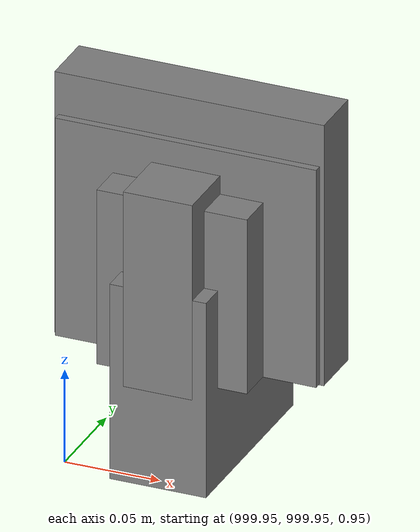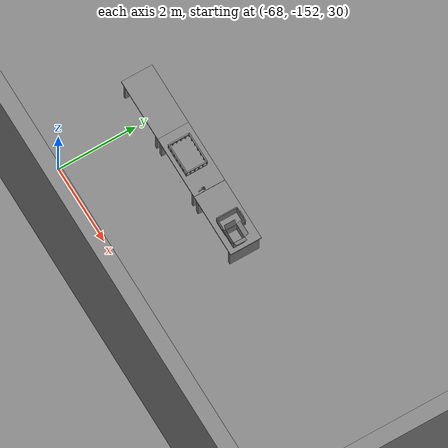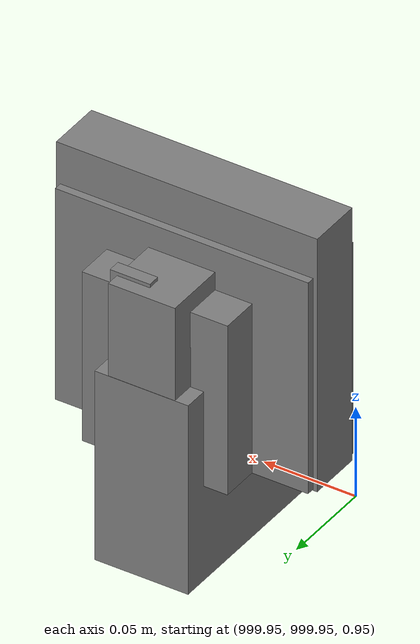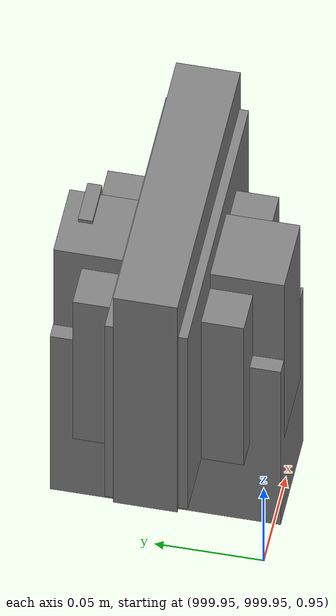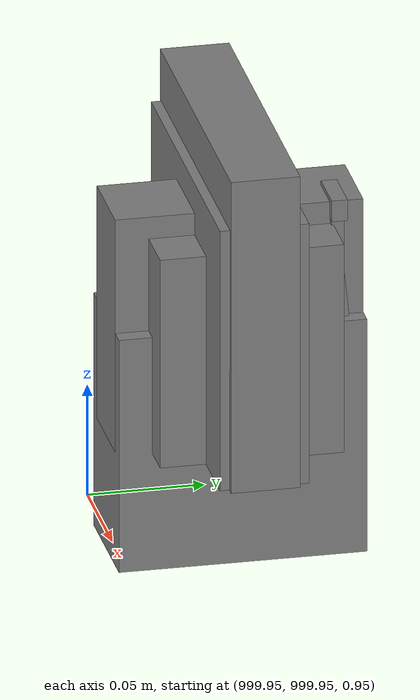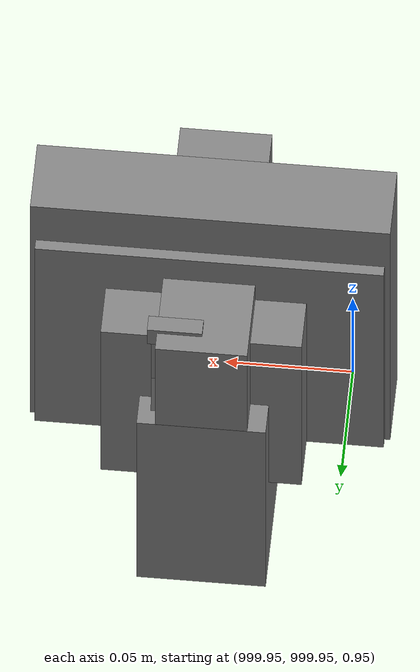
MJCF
<mujoco>
    <option gravity="0.000000000 0.000000000 -9.810000420" timestep="0.0049999999" integrator="implicitfast" density="1.225" viscosity="1.8000001e-05" noslip_iterations="10" iterations="100" sdf_iterations="50">
        <flag multiccd="disable"/>
    </option>
    <size memory="1000M"/>
    <compiler coordinate="local"/>
    <worldbody>
        <light cutoff="30" pos="0 1 1" dir="0 -1 -2"/>
        <light cutoff="30" pos="0 -1 1" dir="0 1 -2"/>
        <body pos="1000.000000000 1000.000000000 1.000000000" euler="0.000011953 0.000005123 -179.999984741" name="openloong_gripper_2f85_fix_base_usda_intel_box">
            <geom contype="1" conaffinity="1" density="1000" type="box" material="" rgba="0.500000000 0.500000000 0.500000000 1.000000000" solimp="0.899999976 0.949999988 0.001000000" friction="1.000000000 0.005000000 0.000100000" solref="0.020000000 1.000000000" margin="0" condim="3" group="0" pos="0.000000000 -0.000067139 0.000082284" quat="0.707106709 0.000000225 0.000000253 0.707106650" size="0.052800003 0.025300000 0.052800003" name="openloong_gripper_2f85_fix_base_usda_geom_09777010_AFED_4B91_A810_9631CA90BC38"/>
            <freejoint name="openloong_gripper_2f85_fix_base_usda_intel_box_joint"/>
            <site size="0.005000000 0.005000000 0.005000000" rgba="0.500000000 0.500000000 0.500000000 1.000000000" pos="0.000000000 0.000000000 0.000000000" quat="0.999961913 0.008726500 0.000000000 0.000000000" group="0" type="sphere" name="openloong_gripper_2f85_fix_base_usda_intel_boxsite"/>
        </body>
        <body pos="-66.033233643 -149.650405884 31.162775040" euler="-51.094249725 21.013368607 63.109119415" mocap="true" name="spotlight1_SpotLight"/>
        <body pos="1000.000000000 1000.000000000 1.000000000" euler="0.000000000 0.000000000 180.000000000" name="openloong_gripper_2f85_fix_base_usda_cpu_fan">
            <geom contype="1" conaffinity="1" density="1000" type="box" material="" rgba="0.500000000 0.500000000 0.500000000 1.000000000" solimp="0.899999976 0.949999988 0.001000000" friction="1.000000000 0.005000000 0.000100000" solref="0.020000000 1.000000000" margin="0" condim="3" group="0" pos="0.000000000 0.000000000 0.070034981" quat="0.000000000 0.000000000 0.000000000 1.000000000" size="0.070700005 0.014699999 0.070700005" name="openloong_gripper_2f85_fix_base_usda_geom_B182E780_EF5A_4C3B_9320_705D481BC3B0"/>
            <freejoint name="openloong_gripper_2f85_fix_base_usda_cpu_fan_joint"/>
            <site size="0.005000000 0.005000000 0.005000000" rgba="0.500000000 0.500000000 0.500000000 1.000000000" pos="0.000000000 0.000000000 0.000000000" quat="0.999961913 0.008726535 0.000000000 0.000000000" group="0" type="sphere" name="openloong_gripper_2f85_fix_base_usda_cpu_fancsite"/>
        </body>
        <body pos="1000.000000000 1000.000000000 1.000000000" euler="0.000000000 0.000000000 180.000000000" name="openloong_gripper_2f85_fix_base_usda_wifi_box">
            <geom contype="1" conaffinity="1" density="1000" type="box" material="" rgba="0.500000000 0.500000000 0.500000000 1.000000000" solimp="0.899999976 0.949999988 0.001000000" friction="1.000000000 0.005000000 0.000100000" solref="0.020000000 1.000000000" margin="0" condim="3" group="0" pos="0.000000000 0.000000000 0.058978677" quat="0.000000000 0.000000047 0.000000000 1.000000000" size="0.068499997 0.018999999 0.059000000" name="openloong_gripper_2f85_fix_base_usda_geom_F771D429_F69C_4782_A052_ED4A63F456D2"/>
            <freejoint name="openloong_gripper_2f85_fix_base_usda_wifi_box_joint"/>
            <site size="0.005000000 0.005000000 0.005000000" rgba="0.500000000 0.500000000 0.500000000 1.000000000" pos="0.000000000 0.000000000 0.000000000" quat="0.999961913 0.008726500 0.000000000 0.000000000" group="0" type="sphere" name="openloong_gripper_2f85_fix_base_usda_wifi_boxsite"/>
        </body>
        <body pos="-66.317672729 -149.536270142 31.162723541" euler="121.390708923 60.162811279 79.176300049" mocap="true" name="spotlight2_SpotLight"/>
        <body pos="1000.000000000 999.999938965 1.000000000" euler="0.000000000 0.000000000 180.000000000" name="openloong_gripper_2f85_fix_base_usda_intelcore_i5">
            <geom contype="1" conaffinity="1" density="1000" type="box" material="" rgba="0.500000000 0.500000000 0.500000000 1.000000000" solimp="0.899999976 0.949999988 0.001000000" friction="1.000000000 0.005000000 0.000100000" solref="0.020000000 1.000000000" margin="0" condim="3" group="0" pos="0.000000000 0.000000000 0.051722717" quat="0.707106709 0.000000000 0.000000000 -0.707106769" size="0.052800000 0.018080002 0.052800000" name="openloong_gripper_2f85_fix_base_usda_geom_7D6B5B0C_A290_4E2B_BD3C_ACD42C3E7C8A"/>
            <freejoint name="openloong_gripper_2f85_fix_base_usda_intelcore_i5_joint"/>
            <site size="0.005000000 0.005000000 0.005000000" rgba="0.500000000 0.500000000 0.500000000 1.000000000" pos="0.000000000 0.000000000 0.000000000" quat="0.999961913 0.008726534 0.000000000 0.000000000" group="0" type="sphere" name="openloong_gripper_2f85_fix_base_usda_intelcore_i5site"/>
        </body>
        <body pos="1000.000000000 1000.000000000 1.000000000" euler="0.000000000 0.000000000 180.000000000" name="openloong_gripper_2f85_fix_base_usda_battery_01">
            <geom contype="1" conaffinity="1" density="1000" type="box" material="" rgba="0.500000000 0.500000000 0.500000000 1.000000000" solimp="0.899999976 0.949999988 0.001000000" friction="1.000000000 0.005000000 0.000100000" solref="0.020000000 1.000000000" margin="0" condim="3" group="0" pos="-0.011123657 -0.041940309 0.101691343" quat="1.000000000 0.000000000 0.000000000 0.000000000" size="0.010800000 0.003375000 0.004725000" name="openloong_gripper_2f85_fix_base_usda_geom_BB0C475E_8F22_472B_B51F_9326C7040ED2"/>
            <geom contype="1" conaffinity="1" density="1000" type="box" material="" rgba="0.500000000 0.500000000 0.500000000 1.000000000" solimp="0.899999976 0.949999988 0.001000000" friction="1.000000000 0.005000000 0.000100000" solref="0.020000000 1.000000000" margin="0" condim="3" group="0" pos="-0.010876465 -0.044247437 0.047066893" quat="0.998702705 -0.050920475 0.000000000 0.000000000" size="0.009450001 0.002700000 0.024975000" name="openloong_gripper_2f85_fix_base_usda_geom_F28FC48F_5AB6_4FE8_970B_5D4833AF08C2"/>
            <geom contype="1" conaffinity="1" density="1000" type="box" material="" rgba="0.500000000 0.500000000 0.500000000 1.000000000" solimp="0.899999976 0.949999988 0.001000000" friction="1.000000000 0.005000000 0.000100000" solref="0.020000000 1.000000000" margin="0" condim="3" group="0" pos="-0.001235962 -0.000659180 0.047381196" quat="1.000000000 0.000000000 0.000000000 0.000000000" size="0.039420001 0.039150000 0.047250003" name="openloong_gripper_2f85_fix_base_usda_geom_872E6619_4E32_41F5_9B57_C917A9D12E42"/>
            <geom contype="1" conaffinity="1" density="1000" type="box" material="" rgba="0.500000000 0.500000000 0.500000000 1.000000000" solimp="0.899999976 0.949999988 0.001000000" friction="1.000000000 0.005000000 0.000100000" solref="0.020000000 1.000000000" margin="0" condim="3" group="0" pos="-0.010876465 -0.039138794 0.009851727" quat="1.000000000 0.000000000 0.000000000 0.000000000" size="0.009450001 0.010800000 0.013500000" name="openloong_gripper_2f85_fix_base_usda_geom_09DAC6A3_9CD4_4563_BCFE_E887D5168C29"/>
            <geom contype="1" conaffinity="1" density="1000" type="box" material="" rgba="0.500000000 0.500000000 0.500000000 1.000000000" solimp="0.899999976 0.949999988 0.001000000" friction="1.000000000 0.005000000 0.000100000" solref="0.020000000 1.000000000" margin="0" condim="3" group="0" pos="-0.010876465 -0.041528322 0.071508206" quat="1.000000000 0.000000000 0.000000000 0.000000000" size="0.009450001 0.002700000 0.027000001" name="openloong_gripper_2f85_fix_base_usda_geom_D125AA8A_AA29_4221_AE42_7A04B3F0A813"/>
            <freejoint name="openloong_gripper_2f85_fix_base_usda_battery_01_joint"/>
            <site size="0.005000000 0.005000000 0.005000000" rgba="0.500000000 0.500000000 0.500000000 1.000000000" pos="0.000000000 0.000000000 0.000000000" quat="0.999961913 0.008726500 0.000000000 0.000000000" group="0" type="sphere" name="openloong_gripper_2f85_fix_base_usda_battery_01site"/>
        </body>
        <body pos="-66.166900635 -148.918640137 31.167116165" euler="65.348434448 -10.535593033 -124.448310852" mocap="true" name="spotlight4_SpotLight"/>
        <body pos="-64.866622925 -149.383972168 30.183746338" euler="89.999984741 89.999946594 0.000000000" name="openloong_gripper_2f85_fix_base_usda_bluebox_01">
            <geom contype="1" conaffinity="1" density="1000" type="box" material="" rgba="0.500000000 0.500000000 0.500000000 1.000000000" solimp="0.899999976 0.949999988 0.001000000" friction="1.000000000 0.005000000 0.000100000" solref="0.020000000 1.000000000" margin="0" condim="3" group="0" pos="0.276580811 0.187225342 0.000068665" quat="0.707106948 0.000077471 0.707106352 0.000077486" size="0.100000001 0.057999998 0.010000000" name="openloong_gripper_2f85_fix_base_usda_geom_EC9F9514_2BE4_4022_A708_59BA21E0713B"/>
            <geom contype="1" conaffinity="1" density="1000" type="box" material="" rgba="0.500000000 0.500000000 0.500000000 1.000000000" solimp="0.899999976 0.949999988 0.001000000" friction="1.000000000 0.005000000 0.000100000" solref="0.020000000 1.000000000" margin="0" condim="3" group="0" pos="0.000000000 0.002883911 0.000000000" quat="0.999999881 0.000000000 0.000000000 0.000000000" size="0.254000008 0.003000000 0.172000006" name="openloong_gripper_2f85_fix_base_usda_geom_55C1155B_A946_4959_9CC0_443E3BAAD244"/>
            <geom contype="1" conaffinity="1" density="1000" type="box" material="" rgba="0.500000000 0.500000000 0.500000000 1.000000000" solimp="0.899999976 0.949999988 0.001000000" friction="1.000000000 0.005000000 0.000100000" solref="0.020000000 1.000000000" margin="0" condim="3" group="0" pos="0.000000000 0.124874115 0.173484802" quat="0.999796331 0.020176515 -0.000000015 0.000000030" size="0.259999990 0.119999997 0.007000000" name="openloong_gripper_2f85_fix_base_usda_geom_199D9C4C_2E50_4F98_A8F4_38D75BB90C2A"/>
            <geom contype="1" conaffinity="1" density="1000" type="box" material="" rgba="0.500000000 0.500000000 0.500000000 1.000000000" solimp="0.899999976 0.949999988 0.001000000" friction="1.000000000 0.005000000 0.000100000" solref="0.020000000 1.000000000" margin="0" condim="3" group="0" pos="0.000000000 0.124874115 -0.173469543" quat="0.999796331 -0.020176545 -0.000000015 0.000000000" size="0.259999990 0.119999997 0.007000000" name="openloong_gripper_2f85_fix_base_usda_geom_56A9C304_0553_4D9D_A745_7E6BBAB7AA1F"/>
            <geom contype="1" conaffinity="1" density="1000" type="box" material="" rgba="0.500000000 0.500000000 0.500000000 1.000000000" solimp="0.899999976 0.949999988 0.001000000" friction="1.000000000 0.005000000 0.000100000" solref="0.020000000 1.000000000" margin="0" condim="3" group="0" pos="0.000000000 0.214008331 0.188980103" quat="0.999912977 0.013176724 0.000000015 0.000000000" size="0.259999990 0.029999999 0.012500000" name="openloong_gripper_2f85_fix_base_usda_geom_94A2BF77_432D_4DA2_81ED_A75655757471"/>
            <geom contype="1" conaffinity="1" density="1000" type="box" material="" rgba="0.500000000 0.500000000 0.500000000 1.000000000" solimp="0.899999976 0.949999988 0.001000000" friction="1.000000000 0.005000000 0.000100000" solref="0.020000000 1.000000000" margin="0" condim="3" group="0" pos="-0.258361816 0.125289917 0.001876831" quat="0.702796936 -0.020792112 0.710783124 0.020769298" size="0.189999998 0.119999997 0.009000000" name="openloong_gripper_2f85_fix_base_usda_geom_AB55458F_A8AB_457E_A308_3127DC3312A1"/>
            <geom contype="1" conaffinity="1" density="1000" type="box" material="" rgba="0.500000000 0.500000000 0.500000000 1.000000000" solimp="0.899999976 0.949999988 0.001000000" friction="1.000000000 0.005000000 0.000100000" solref="0.020000000 1.000000000" margin="0" condim="3" group="0" pos="0.000000000 0.214008331 -0.188980103" quat="0.999912977 -0.013176769 0.000000030 0.000000015" size="0.259999990 0.029999999 0.012500000" name="openloong_gripper_2f85_fix_base_usda_geom_A5F4BE9A_3A01_4880_A960_D15C3AF57529"/>
            <geom contype="1" conaffinity="1" density="1000" type="box" material="" rgba="0.500000000 0.500000000 0.500000000 1.000000000" solimp="0.899999976 0.949999988 0.001000000" friction="1.000000000 0.005000000 0.000100000" solref="0.020000000 1.000000000" margin="0" condim="3" group="0" pos="-0.276611328 0.187225342 0.000068665" quat="0.707106650 0.000077441 0.707106709 0.000077456" size="0.100000001 0.057999998 0.010000000" name="openloong_gripper_2f85_fix_base_usda_geom_52CA0E83_47AD_48C4_B1BA_9AA388338E3F"/>
            <geom contype="1" conaffinity="1" density="1000" type="box" material="" rgba="0.500000000 0.500000000 0.500000000 1.000000000" solimp="0.899999976 0.949999988 0.001000000" friction="1.000000000 0.005000000 0.000100000" solref="0.020000000 1.000000000" margin="0" condim="3" group="0" pos="0.258331299 0.125289917 0.001876831" quat="0.702851415 0.018856421 0.710823774 -0.019329369" size="0.189999998 0.119999997 0.009000000" name="openloong_gripper_2f85_fix_base_usda_geom_317BC661_5F4E_4F97_B510_B66BB8F2E911"/>
            <freejoint name="openloong_gripper_2f85_fix_base_usda_bluebox_01_joint"/>
            <site size="0.005000000 0.005000000 0.005000000" rgba="0.500000000 0.500000000 0.500000000 1.000000000" pos="0.000000000 0.000000000 0.000000000" quat="0.999961913 0.008726534 0.000000000 0.000000000" group="0" type="sphere" name="openloong_gripper_2f85_fix_base_usda_bluebox_01site"/>
        </body>
        <body pos="-64.496299744 -149.491867065 30.235729218" euler="0.000000000 0.000000000 89.999946594" name="openloong_gripper_2f85_fix_base_usda_cardboardbox_01">
            <geom contype="1" conaffinity="1" density="1000" type="box" material="" rgba="0.500000000 0.500000000 0.500000000 1.000000000" solimp="0.899999976 0.949999988 0.001000000" friction="1.000000000 0.005000000 0.000100000" solref="0.020000000 1.000000000" margin="0" condim="3" group="0" pos="-0.003166199 -0.004086494 0.005052090" quat="1.000000000 0.000000000 0.000000000 0.000000000" size="0.142499998 0.177500010 0.005000000" name="openloong_gripper_2f85_fix_base_usda_geom_502548B2_F18C_40A9_9DD2_326F187D1B8C"/>
            <geom contype="1" conaffinity="1" density="1000" type="box" material="" rgba="0.500000000 0.500000000 0.500000000 1.000000000" solimp="0.899999976 0.949999988 0.001000000" friction="1.000000000 0.005000000 0.000100000" solref="0.020000000 1.000000000" margin="0" condim="3" group="0" pos="-0.003166199 0.170316696 0.150570869" quat="1.000000000 0.000000000 0.000000000 0.000000000" size="0.142499998 0.005000000 0.149999991" name="openloong_gripper_2f85_fix_base_usda_geom_5E0AD782_05BB_499E_98D4_0934322EFC1A"/>
            <geom contype="1" conaffinity="1" density="1000" type="box" material="" rgba="0.500000000 0.500000000 0.500000000 1.000000000" solimp="0.899999976 0.949999988 0.001000000" friction="1.000000000 0.005000000 0.000100000" solref="0.020000000 1.000000000" margin="0" condim="3" group="0" pos="-0.147399902 -0.005307198 0.150570869" quat="1.000000000 0.000000000 0.000000000 0.000000000" size="0.005000000 0.177500010 0.149999991" name="openloong_gripper_2f85_fix_base_usda_geom_71427CCC_3EA4_4DB6_BE0A_1506FD5322F9"/>
            <geom contype="1" conaffinity="1" density="1000" type="box" material="" rgba="0.500000000 0.500000000 0.500000000 1.000000000" solimp="0.899999976 0.949999988 0.001000000" friction="1.000000000 0.005000000 0.000100000" solref="0.020000000 1.000000000" margin="0" condim="3" group="0" pos="0.140275955 -0.005307198 0.150570869" quat="1.000000000 0.000000000 0.000000000 0.000000000" size="0.005000000 0.177500010 0.149999991" name="openloong_gripper_2f85_fix_base_usda_geom_7DDAF8C2_266F_4E6D_B4F6_4088F7710903"/>
            <geom contype="1" conaffinity="1" density="1000" type="box" material="" rgba="0.500000000 0.500000000 0.500000000 1.000000000" solimp="0.899999976 0.949999988 0.001000000" friction="1.000000000 0.005000000 0.000100000" solref="0.020000000 1.000000000" margin="0" condim="3" group="0" pos="-0.003166199 -0.181550980 0.150570869" quat="1.000000000 0.000000000 0.000000000 0.000000000" size="0.142499998 0.005000000 0.149999991" name="openloong_gripper_2f85_fix_base_usda_geom_7A09CE59_A3DF_43FD_848E_A6AE4BDF7136"/>
            <freejoint name="openloong_gripper_2f85_fix_base_usda_cardboardbox_01_joint"/>
            <site size="0.005000000 0.005000000 0.005000000" rgba="0.500000000 0.500000000 0.500000000 1.000000000" pos="0.000000000 0.000000000 0.000000000" quat="0.999961913 0.008726535 0.000000000 0.000000000" group="0" type="sphere" name="openloong_gripper_2f85_fix_base_usda_site_B069072B_4BBD_47FB_9B6B_FE7A82207B3E"/>
            <body pos="0.139160156 -0.004048347 0.301930904" euler="-179.999954224 49.383502960 179.999954224" name="openloong_gripper_2f85_fix_base_usda_A1_006">
                <geom contype="1" conaffinity="1" density="1000" type="box" material="" rgba="0.500000000 0.500000000 0.500000000 1.000000000" solimp="0.899999976 0.949999988 0.001000000" friction="1.000000000 0.005000000 0.000100000" solref="0.020000000 1.000000000" margin="0" condim="3" group="0" pos="-0.071587563 0.000009537 0.001745224" quat="0.999999881 0.000000000 0.000000000 0.000000000" size="0.071249999 0.179999992 0.002500000" name="openloong_gripper_2f85_fix_base_usda_geom_F248FDAD_DE66_4023_9045_E3C689F0FAD0"/>
                <joint armature="0" stiffness="0.07" damping="0.0099999998" axis="0.000000 1.000000 0.000000" type="hinge" name="openloong_gripper_2f85_fix_base_usda_A1_006"/>
            </body>
            <body pos="-0.145902634 -0.004086494 0.301938057" euler="-180.000000000 -60.000011444 -180.000000000" name="openloong_gripper_2f85_fix_base_usda_A2_006">
                <geom contype="1" conaffinity="1" density="1000" type="box" material="" rgba="0.500000000 0.500000000 0.500000000 1.000000000" solimp="0.899999976 0.949999988 0.001000000" friction="1.000000000 0.005000000 0.000100000" solref="0.020000000 1.000000000" margin="0" condim="3" group="0" pos="0.071268082 0.000009537 0.002717972" quat="0.000002921 0.000000000 -0.000000030 0.999999881" size="0.071249999 0.179999992 0.002500000" name="openloong_gripper_2f85_fix_base_usda_geom_0EACB3F4_9BDD_45B3_9F37_697A877654D2"/>
                <joint armature="0" stiffness="0.07" damping="0.0099999998" axis="0.000000 1.000000 0.000000" type="hinge" name="openloong_gripper_2f85_fix_base_usda_A2_006"/>
            </body>
            <body pos="-0.003385544 0.175991058 0.301930904" euler="-125.858116150 -0.000004561 0.000002331" name="openloong_gripper_2f85_fix_base_usda_B2_006">
                <geom contype="1" conaffinity="1" density="1000" type="box" material="" rgba="0.500000000 0.500000000 0.500000000 1.000000000" solimp="0.899999976 0.949999988 0.001000000" friction="1.000000000 0.005000000 0.000100000" solref="0.020000000 1.000000000" margin="0" condim="3" group="0" pos="0.000009537 -0.070939064 -0.002470016" quat="0.999614120 0.027776197 -0.000000015 0.000000030" size="0.137500003 0.064999998 0.005000000" name="openloong_gripper_2f85_fix_base_usda_geom_D8DFABF9_164B_463E_B4B6_E6189E6ED429"/>
                <joint armature="0" stiffness="0.07" damping="0.0099999998" axis="1.000000 0.000000 0.000000" type="hinge" name="openloong_gripper_2f85_fix_base_usda_B2_006"/>
            </body>
            <body pos="-0.003385544 -0.184140205 0.301938057" euler="147.805557251 0.000000000 0.000000000" name="openloong_gripper_2f85_fix_base_usda_B1_006">
                <geom contype="1" conaffinity="1" density="1000" type="box" material="" rgba="0.500000000 0.500000000 0.500000000 1.000000000" solimp="0.899999976 0.949999988 0.001000000" friction="1.000000000 0.005000000 0.000100000" solref="0.020000000 1.000000000" margin="0" condim="3" group="0" pos="-0.000028610 0.070202351 -0.002703667" quat="0.999614179 -0.027776167 0.000000000 0.000000000" size="0.137500003 0.064999998 0.005000000" name="openloong_gripper_2f85_fix_base_usda_geom_80AAF5A0_C9D4_406E_AC2A_5BE4849D20EE"/>
                <joint armature="0" stiffness="0.07" damping="0.0099999998" axis="1.000000 0.000000 0.000000" type="hinge" name="openloong_gripper_2f85_fix_base_usda_B1_006"/>
            </body>
        </body>
        <body pos="-65.882858276 -149.481979370 30.229999542" euler="-64.487716675 0.000000000 0.000000000" name="openloong_gripper_2f85_fix_base_usda_Barcode">
            <geom contype="1" conaffinity="1" density="1000" type="box" material="" rgba="0.500000000 0.500000000 0.500000000 1.000000000" solimp="0.899999976 0.949999988 0.001000000" friction="1.000000000 0.005000000 0.000100000" solref="0.020000000 1.000000000" margin="0" condim="3" group="0" pos="0.000000000 0.013038635 0.001419067" quat="0.000000000 0.000000000 0.000000000 1.000000119" size="0.034000002 0.010000000 0.017999999" name="openloong_gripper_2f85_fix_base_usda_geom_D6852C08_69B0_49AE_B183_3FEB9E9669D9"/>
            <geom contype="1" conaffinity="1" density="1000" type="box" material="" rgba="0.500000000 0.500000000 0.500000000 1.000000000" solimp="0.899999976 0.949999988 0.001000000" friction="1.000000000 0.005000000 0.000100000" solref="0.020000000 1.000000000" margin="0" condim="3" group="0" pos="0.000000000 -0.035301208 -0.007095337" quat="0.000000000 0.000000000 -0.043619365 0.999048233" size="0.028999999 0.010000000 0.020000000" name="openloong_gripper_2f85_fix_base_usda_geom_E8951E4A_1049_4EE9_AD26_BC12A8462A7B"/>
            <geom contype="1" conaffinity="1" density="1000" type="box" material="" rgba="0.500000000 0.500000000 0.500000000 1.000000000" solimp="0.899999976 0.949999988 0.001000000" friction="1.000000000 0.005000000 0.000100000" solref="0.020000000 1.000000000" margin="0" condim="3" group="0" pos="0.000000000 -0.043411255 -0.011749268" quat="0.922262907 0.386563420 0.000000000 0.000000000" size="0.026000001 0.010000000 0.020000000" name="openloong_gripper_2f85_fix_base_usda_geom_CEE6FB1D_F75A_414D_B42F_E13D6FE96AE3"/>
            <geom contype="1" conaffinity="1" density="1000" type="box" material="" rgba="0.500000000 0.500000000 0.500000000 1.000000000" solimp="0.899999976 0.949999988 0.001000000" friction="1.000000000 0.005000000 0.000100000" solref="0.020000000 1.000000000" margin="0" condim="3" group="0" pos="0.000000000 -0.016967773 -0.031860352" quat="0.000000000 0.000000000 0.000000000 1.000000119" size="0.008000000 0.010000000 0.013000000" name="openloong_gripper_2f85_fix_base_usda_geom_470CB80D_AB99_42A7_9E51_3DC1B1C1E454"/>
            <geom contype="1" conaffinity="1" density="1000" type="box" material="" rgba="0.500000000 0.500000000 0.500000000 1.000000000" solimp="0.899999976 0.949999988 0.001000000" friction="1.000000000 0.005000000 0.000100000" solref="0.020000000 1.000000000" margin="0" condim="3" group="0" pos="0.000000000 -0.001869202 0.000312805" quat="0.953716993 0.300705761 0.000000000 0.000000000" size="0.032000002 0.010000000 0.018999999" name="openloong_gripper_2f85_fix_base_usda_geom_137296B3_914C_448E_A9E8_1980C7B4EEDD"/>
            <geom contype="1" conaffinity="1" density="1000" type="box" material="" rgba="0.500000000 0.500000000 0.500000000 1.000000000" solimp="0.899999976 0.949999988 0.001000000" friction="1.000000000 0.005000000 0.000100000" solref="0.020000000 1.000000000" margin="0" condim="3" group="0" pos="0.000000000 -0.019531250 -0.003173828" quat="0.953716993 0.300705761 0.000000000 0.000000000" size="0.030999999 0.010000000 0.020000000" name="openloong_gripper_2f85_fix_base_usda_geom_44A70EC2_800D_4989_9167_80953ED920EA"/>
            <geom contype="1" conaffinity="1" density="1000" type="box" material="" rgba="0.500000000 0.500000000 0.500000000 1.000000000" solimp="0.899999976 0.949999988 0.001000000" friction="1.000000000 0.005000000 0.000100000" solref="0.020000000 1.000000000" margin="0" condim="3" group="0" pos="0.000000000 -0.035301208 -0.007095337" quat="0.953716993 0.300705761 0.000000000 0.000000000" size="0.028999999 0.010000000 0.020000000" name="openloong_gripper_2f85_fix_base_usda_geom_D7AFC057_7984_46CA_8C18_7F80CEB953AE"/>
            <geom contype="1" conaffinity="1" density="1000" type="box" material="" rgba="0.500000000 0.500000000 0.500000000 1.000000000" solimp="0.899999976 0.949999988 0.001000000" friction="1.000000000 0.005000000 0.000100000" solref="0.020000000 1.000000000" margin="0" condim="3" group="0" pos="0.000000000 -0.042617798 -0.071121216" quat="0.000000000 0.000000000 0.000000000 1.000000119" size="0.013000000 0.021000000 0.059999999" name="openloong_gripper_2f85_fix_base_usda_geom_67D26B02_9275_465E_B484_4D16A961261B"/>
            <freejoint name="openloong_gripper_2f85_fix_base_usda_Barcode_joint"/>
            <site size="0.005000000 0.005000000 0.005000000" rgba="0.500000000 0.500000000 0.500000000 1.000000000" pos="0.000000000 0.000000000 0.000000000" quat="1.000000000 0.000000000 0.000000000 0.000000000" group="0" type="sphere" name="openloong_gripper_2f85_fix_base_usda_Barcode_site"/>
        </body>
        <body pos="-66.745018005 -149.392349243 30.184000015" euler="0.000000000 0.000000000 89.999946594" name="[22333154799700]_Basket_01">
            <geom contype="1" conaffinity="1" density="1000" type="box" material="" rgba="0.500000000 0.500000000 0.500000000 1.000000000" solimp="0.899999976 0.949999988 0.001000000" friction="1.000000000 0.005000000 0.000100000" solref="0.020000000 1.000000000" margin="0" condim="3" group="0" pos="-0.052425385 0.389207840 0.089787483" quat="0.707107008 0.000000000 0.000000000 0.707106411" size="0.014249999 0.014249999 0.059999999" name="[22333154799700]_geom_51764691_2C6E_4B7B_878D_7148267AE8DF"/>
            <geom contype="1" conaffinity="1" density="1000" type="box" material="" rgba="0.500000000 0.500000000 0.500000000 1.000000000" solimp="0.899999976 0.949999988 0.001000000" friction="1.000000000 0.005000000 0.000100000" solref="0.020000000 1.000000000" margin="0" condim="3" group="0" pos="0.264015198 -0.133043289 0.089787483" quat="0.707107008 0.000000000 0.000000000 0.707106411" size="0.014249999 0.014249999 0.059999999" name="[22333154799700]_geom_7F2116CA_1263_4179_A29B_C0CE35F5669B"/>
            <geom contype="1" conaffinity="1" density="1000" type="box" material="" rgba="0.500000000 0.500000000 0.500000000 1.000000000" solimp="0.899999976 0.949999988 0.001000000" friction="1.000000000 0.005000000 0.000100000" solref="0.020000000 1.000000000" margin="0" condim="3" group="0" pos="-0.264015198 -0.265548706 0.089793205" quat="0.707107008 0.000000000 0.000000000 0.707106411" size="0.014249999 0.014249999 0.059999999" name="[22333154799700]_geom_0EDD5EA0_A21F_4F06_BCDC_C5C50210C6EC"/>
            <geom contype="1" conaffinity="1" density="1000" type="box" material="" rgba="0.500000000 0.500000000 0.500000000 1.000000000" solimp="0.899999976 0.949999988 0.001000000" friction="1.000000000 0.005000000 0.000100000" solref="0.020000000 1.000000000" margin="0" condim="3" group="0" pos="-0.160263062 -0.389322281 0.089793205" quat="0.707107008 0.000000000 0.000000000 0.707106411" size="0.014249999 0.014249999 0.059999999" name="[22333154799700]_geom_9EDC98AE_E64B_48B9_AEEA_6A7A50151A62"/>
            <geom contype="1" conaffinity="1" density="1000" type="box" material="" rgba="0.500000000 0.500000000 0.500000000 1.000000000" solimp="0.899999976 0.949999988 0.001000000" friction="1.000000000 0.005000000 0.000100000" solref="0.020000000 1.000000000" margin="0" condim="3" group="0" pos="0.162265778 -0.389322281 0.089787483" quat="0.707107008 0.000000000 0.000000000 0.707106411" size="0.014249999 0.014249999 0.059999999" name="[22333154799700]_geom_80CBCAAA_2DA4_4E22_8953_A0A2D8361571"/>
            <geom contype="1" conaffinity="1" density="1000" type="box" material="" rgba="0.500000000 0.500000000 0.500000000 1.000000000" solimp="0.899999976 0.949999988 0.001000000" friction="1.000000000 0.005000000 0.000100000" solref="0.020000000 1.000000000" margin="0" condim="3" group="0" pos="0.264015198 0.389207840 0.089787483" quat="0.707107008 0.000000000 0.000000000 0.707106411" size="0.014249999 0.014249999 0.059999999" name="[22333154799700]_geom_F5C0895C_174F_4C29_BA80_CB312A8C1C3D"/>
            <geom contype="1" conaffinity="1" density="1000" type="box" material="" rgba="0.500000000 0.500000000 0.500000000 1.000000000" solimp="0.899999976 0.949999988 0.001000000" friction="1.000000000 0.005000000 0.000100000" solref="0.020000000 1.000000000" margin="0" condim="3" group="0" pos="-0.264015198 -0.133043289 0.089793205" quat="0.707107008 0.000000000 0.000000000 0.707106411" size="0.014249999 0.014249999 0.059999999" name="[22333154799700]_geom_F5D1C1D4_FD7C_4C57_AE9C_935C4CCAAF97"/>
            <geom contype="1" conaffinity="1" density="1000" type="box" material="" rgba="0.500000000 0.500000000 0.500000000 1.000000000" solimp="0.899999976 0.949999988 0.001000000" friction="1.000000000 0.005000000 0.000100000" solref="0.020000000 1.000000000" margin="0" condim="3" group="0" pos="-0.264026642 0.269256592 0.089793205" quat="0.707107008 0.000000000 0.000000000 0.707106411" size="0.014249999 0.014249999 0.059999999" name="[22333154799700]_geom_4DC3882C_3792_4B4A_BCF2_E5445E1D270D"/>
            <geom contype="1" conaffinity="1" density="1000" type="box" material="" rgba="0.500000000 0.500000000 0.500000000 1.000000000" solimp="0.899999976 0.949999988 0.001000000" friction="1.000000000 0.005000000 0.000100000" solref="0.020000000 1.000000000" margin="0" condim="3" group="0" pos="0.054462433 0.389207840 0.089787483" quat="0.707107008 0.000000000 0.000000000 0.707106411" size="0.014249999 0.014249999 0.059999999" name="[22333154799700]_geom_EC85A906_7D7C_492C_9F9F_3F829E341952"/>
            <geom contype="1" conaffinity="1" density="1000" type="box" material="" rgba="0.500000000 0.500000000 0.500000000 1.000000000" solimp="0.899999976 0.949999988 0.001000000" friction="1.000000000 0.005000000 0.000100000" solref="0.020000000 1.000000000" margin="0" condim="3" group="0" pos="0.054462433 -0.389322281 0.089787483" quat="0.707107008 0.000000000 0.000000000 0.707106411" size="0.014249999 0.014249999 0.059999999" name="[22333154799700]_geom_E708970E_4BB5_4324_8678_B1D99F711464"/>
            <geom contype="1" conaffinity="1" density="1000" type="box" material="" rgba="0.500000000 0.500000000 0.500000000 1.000000000" solimp="0.899999976 0.949999988 0.001000000" friction="1.000000000 0.005000000 0.000100000" solref="0.020000000 1.000000000" margin="0" condim="3" group="0" pos="0.264015198 0.269256592 0.089793205" quat="0.707107008 0.000000000 0.000000000 0.707106411" size="0.014249999 0.014249999 0.059999999" name="[22333154799700]_geom_7250B5E8_7AC7_4601_AE07_8D5008554B65"/>
            <geom contype="1" conaffinity="1" density="1000" type="box" material="" rgba="0.500000000 0.500000000 0.500000000 1.000000000" solimp="0.899999976 0.949999988 0.001000000" friction="1.000000000 0.005000000 0.000100000" solref="0.020000000 1.000000000" margin="0" condim="3" group="0" pos="0.264015198 -0.389322281 0.089787483" quat="0.707107008 0.000000000 0.000000000 0.707106411" size="0.014249999 0.014249999 0.059999999" name="[22333154799700]_geom_51CC7345_FB2B_4A51_A04B_3D6F9FDC1888"/>
            <geom contype="1" conaffinity="1" density="1000" type="box" material="" rgba="0.500000000 0.500000000 0.500000000 1.000000000" solimp="0.899999976 0.949999988 0.001000000" friction="1.000000000 0.005000000 0.000100000" solref="0.020000000 1.000000000" margin="0" condim="3" group="0" pos="0.000000000 0.000000000 0.015998840" quat="0.707107008 0.000000000 0.000000000 0.707106411" size="0.403499991 0.279000014 0.015750000" name="[22333154799700]_geom_22051B1E_F2AF_404A_A438_FB3B0A555EDE"/>
            <geom contype="1" conaffinity="1" density="1000" type="box" material="" rgba="0.500000000 0.500000000 0.500000000 1.000000000" solimp="0.899999976 0.949999988 0.001000000" friction="1.000000000 0.005000000 0.000100000" solref="0.020000000 1.000000000" margin="0" condim="3" group="0" pos="0.000000000 -0.389476776 0.163619041" quat="0.707107008 0.000000000 0.000000000 0.707106411" size="0.015000000 0.277500004 0.015750000" name="[22333154799700]_geom_009337E5_9541_4F58_8777_8FD50FD9D99A"/>
            <geom contype="1" conaffinity="1" density="1000" type="box" material="" rgba="0.500000000 0.500000000 0.500000000 1.000000000" solimp="0.899999976 0.949999988 0.001000000" friction="1.000000000 0.005000000 0.000100000" solref="0.020000000 1.000000000" margin="0" condim="3" group="0" pos="0.162265778 0.389207840 0.089787483" quat="0.707107008 0.000000000 0.000000000 0.707106411" size="0.014249999 0.014249999 0.059999999" name="[22333154799700]_geom_0BCC312B_294A_4B47_A5C4_87E573CFB2F1"/>
            <geom contype="1" conaffinity="1" density="1000" type="box" material="" rgba="0.500000000 0.500000000 0.500000000 1.000000000" solimp="0.899999976 0.949999988 0.001000000" friction="1.000000000 0.005000000 0.000100000" solref="0.020000000 1.000000000" margin="0" condim="3" group="0" pos="0.000000000 0.389471054 0.163619041" quat="0.707107008 0.000000000 0.000000000 0.707106411" size="0.015000000 0.277500004 0.015750000" name="[22333154799700]_geom_9EC01984_7763_49EC_8AFB_97835495D4ED"/>
            <geom contype="1" conaffinity="1" density="1000" type="box" material="" rgba="0.500000000 0.500000000 0.500000000 1.000000000" solimp="0.899999976 0.949999988 0.001000000" friction="1.000000000 0.005000000 0.000100000" solref="0.020000000 1.000000000" margin="0" condim="3" group="0" pos="-0.263511658 0.000000000 0.163619041" quat="0.707107008 0.000000000 0.000000000 0.707106411" size="0.403499991 0.015000000 0.015750000" name="[22333154799700]_geom_3C96D316_5208_4C52_A60B_AE7E227BE20C"/>
            <geom contype="1" conaffinity="1" density="1000" type="box" material="" rgba="0.500000000 0.500000000 0.500000000 1.000000000" solimp="0.899999976 0.949999988 0.001000000" friction="1.000000000 0.005000000 0.000100000" solref="0.020000000 1.000000000" margin="0" condim="3" group="0" pos="-0.264015198 0.141334534 0.089793205" quat="0.707107008 0.000000000 0.000000000 0.707106411" size="0.014249999 0.014249999 0.059999999" name="[22333154799700]_geom_0DD56FFF_95AC_401D_A188_C6589F4707E8"/>
            <geom contype="1" conaffinity="1" density="1000" type="box" material="" rgba="0.500000000 0.500000000 0.500000000 1.000000000" solimp="0.899999976 0.949999988 0.001000000" friction="1.000000000 0.005000000 0.000100000" solref="0.020000000 1.000000000" margin="0" condim="3" group="0" pos="0.264015198 -0.265548706 0.089787483" quat="0.707107008 0.000000000 0.000000000 0.707106411" size="0.014249999 0.014249999 0.059999999" name="[22333154799700]_geom_A9637843_310C_48BE_8C94_BAC6721C7F5C"/>
            <geom contype="1" conaffinity="1" density="1000" type="box" material="" rgba="0.500000000 0.500000000 0.500000000 1.000000000" solimp="0.899999976 0.949999988 0.001000000" friction="1.000000000 0.005000000 0.000100000" solref="0.020000000 1.000000000" margin="0" condim="3" group="0" pos="-0.160263062 0.389207840 0.089787483" quat="0.707107008 0.000000000 0.000000000 0.707106411" size="0.014249999 0.014249999 0.059999999" name="[22333154799700]_geom_360EF772_80AD_405D_8202_F342F16D980B"/>
            <geom contype="1" conaffinity="1" density="1000" type="box" material="" rgba="0.500000000 0.500000000 0.500000000 1.000000000" solimp="0.899999976 0.949999988 0.001000000" friction="1.000000000 0.005000000 0.000100000" solref="0.020000000 1.000000000" margin="0" condim="3" group="0" pos="-0.052425385 -0.389322281 0.089787483" quat="0.707107008 0.000000000 0.000000000 0.707106411" size="0.014249999 0.014249999 0.059999999" name="[22333154799700]_geom_BD09F7E4_E863_4521_8107_91C4DC88EDAE"/>
            <geom contype="1" conaffinity="1" density="1000" type="box" material="" rgba="0.500000000 0.500000000 0.500000000 1.000000000" solimp="0.899999976 0.949999988 0.001000000" friction="1.000000000 0.005000000 0.000100000" solref="0.020000000 1.000000000" margin="0" condim="3" group="0" pos="-0.264026642 -0.389322281 0.089793205" quat="0.707107008 0.000000000 0.000000000 0.707106411" size="0.014249999 0.014249999 0.059999999" name="[22333154799700]_geom_BBE4A36E_A0B1_40DE_903D_BC736A2151C4"/>
            <geom contype="1" conaffinity="1" density="1000" type="box" material="" rgba="0.500000000 0.500000000 0.500000000 1.000000000" solimp="0.899999976 0.949999988 0.001000000" friction="1.000000000 0.005000000 0.000100000" solref="0.020000000 1.000000000" margin="0" condim="3" group="0" pos="0.264015198 0.141334534 0.089787483" quat="0.707107008 0.000000000 0.000000000 0.707106411" size="0.014249999 0.014249999 0.059999999" name="[22333154799700]_geom_151AAE89_AED3_4A42_91D9_54D3F5D02586"/>
            <geom contype="1" conaffinity="1" density="1000" type="box" material="" rgba="0.500000000 0.500000000 0.500000000 1.000000000" solimp="0.899999976 0.949999988 0.001000000" friction="1.000000000 0.005000000 0.000100000" solref="0.020000000 1.000000000" margin="0" condim="3" group="0" pos="-0.264015198 0.389207840 0.089793205" quat="0.707107008 0.000000000 0.000000000 0.707106411" size="0.014249999 0.014249999 0.059999999" name="[22333154799700]_geom_828EA8C2_CF4A_4BD4_B40A_2B0463A440B1"/>
            <geom contype="1" conaffinity="1" density="1000" type="box" material="" rgba="0.500000000 0.500000000 0.500000000 1.000000000" solimp="0.899999976 0.949999988 0.001000000" friction="1.000000000 0.005000000 0.000100000" solref="0.020000000 1.000000000" margin="0" condim="3" group="0" pos="0.264015198 0.004480362 0.089787483" quat="0.707107008 0.000000000 0.000000000 0.707106411" size="0.014249999 0.014249999 0.059999999" name="[22333154799700]_geom_DFEEBE7B_8F26_441F_837A_391D18EA7A4C"/>
            <geom contype="1" conaffinity="1" density="1000" type="box" material="" rgba="0.500000000 0.500000000 0.500000000 1.000000000" solimp="0.899999976 0.949999988 0.001000000" friction="1.000000000 0.005000000 0.000100000" solref="0.020000000 1.000000000" margin="0" condim="3" group="0" pos="0.263694763 -0.000011444 0.163619041" quat="0.707107008 0.000000000 0.000000000 0.707106411" size="0.403499991 0.015000000 0.015750000" name="[22333154799700]_geom_F54E8B5C_D197_46DF_B262_B39534CCDB27"/>
            <geom contype="1" conaffinity="1" density="1000" type="box" material="" rgba="0.500000000 0.500000000 0.500000000 1.000000000" solimp="0.899999976 0.949999988 0.001000000" friction="1.000000000 0.005000000 0.000100000" solref="0.020000000 1.000000000" margin="0" condim="3" group="0" pos="-0.264015198 0.004480362 0.089793205" quat="0.707107008 0.000000000 0.000000000 0.707106411" size="0.014249999 0.014249999 0.059999999" name="[22333154799700]_geom_7D030542_4E22_4882_BB51_1081E603F36E"/>
            <freejoint name="[22333154799700]_joint_2AED701F_EAC8_4C66_9C00_AF5119807786"/>
        </body>
        <body pos="0.000000000 0.000000000 0.000000000" euler="0.000000000 0.000000000 0.000000000" name="Static Objects_Static Objects">
            <geom contype="1" conaffinity="1" density="1000" type="box" material="" rgba="0.500000000 0.500000000 0.500000000 1.000000000" solimp="0.899999976 0.949999988 0.001000000" friction="1.000000000 0.005000000 0.000100000" solref="0.020000000 1.000000000" margin="0" condim="3" group="0" pos="-67.544113159 -149.365814209 29.727830887" quat="0.500000417 0.499999970 0.499999553 0.499999970" size="0.381000012 0.319999993 0.041000001" name="Static Objects_geom_7A70652A_FCAE_4907_B3A5_FE5120E5DA64"/>
            <geom contype="1" conaffinity="1" density="1000" type="box" material="" rgba="0.500000000 0.500000000 0.500000000 1.000000000" solimp="0.899999976 0.949999988 0.001000000" friction="1.000000000 0.005000000 0.000100000" solref="0.020000000 1.000000000" margin="0" condim="3" group="0" pos="-68.239501953 -149.365814209 30.086868286" quat="0.500000417 0.499999970 0.499999553 0.499999970" size="0.370999992 0.039500002 0.745000005" name="Static Objects_geom_838AC25C_BD7A_47C5_980B_7A372A51A478"/>
            <geom contype="1" conaffinity="1" density="1000" type="box" material="" rgba="0.500000000 0.500000000 0.500000000 1.000000000" solimp="0.899999976 0.949999988 0.001000000" friction="1.000000000 0.005000000 0.000100000" solref="0.020000000 1.000000000" margin="0" condim="3" group="0" pos="-68.239501953 -149.365814209 30.147235870" quat="0.500000417 0.499999970 0.499999553 0.499999970" size="0.400000006 0.022000000 0.800000012" name="Static Objects_geom_41A58C91_B21F_4981_B96B_0C1F9A75AFE9"/>
            <geom contype="1" conaffinity="1" density="1000" type="box" material="" rgba="0.500000000 0.500000000 0.500000000 1.000000000" solimp="0.899999976 0.949999988 0.001000000" friction="1.000000000 0.005000000 0.000100000" solref="0.020000000 1.000000000" margin="0" condim="3" group="0" pos="-68.934890747 -149.365814209 29.727830887" quat="0.500000417 0.499999970 0.499999553 0.499999970" size="0.381000012 0.319999993 0.041000001" name="Static Objects_geom_E86AF4C5_1913_4474_9298_8155D96901E9"/>
            <geom contype="1" conaffinity="1" density="1000" type="box" material="" rgba="0.500000000 0.500000000 0.500000000 1.000000000" solimp="0.899999976 0.949999988 0.001000000" friction="1.000000000 0.005000000 0.000100000" solref="0.020000000 1.000000000" margin="0" condim="3" group="0" pos="-68.239501953 -149.365814209 29.561563492" quat="0.500000417 0.499999970 0.499999553 0.499999970" size="0.020000000 0.022000000 0.660000026" name="Static Objects_geom_8D0470CD_1684_49E9_8165_E5BE171BDD71"/>
            <geom contype="1" conaffinity="1" density="1000" type="box" material="" rgba="0.500000000 0.500000000 0.500000000 1.000000000" solimp="0.899999976 0.949999988 0.001000000" friction="1.000000000 0.005000000 0.000100000" solref="0.020000000 1.000000000" margin="0" condim="3" group="0" pos="-65.945671082 -149.365814209 29.727830887" quat="0.500000417 0.499999970 0.499999553 0.499999970" size="0.381000012 0.319999993 0.041000001" name="Static Objects_geom_500F1EA5_52AB_47B9_BF1B_74AA001CE417"/>
            <geom contype="1" conaffinity="1" density="1000" type="box" material="" rgba="0.500000000 0.500000000 0.500000000 1.000000000" solimp="0.899999976 0.949999988 0.001000000" friction="1.000000000 0.005000000 0.000100000" solref="0.020000000 1.000000000" margin="0" condim="3" group="0" pos="-66.641059875 -149.365814209 30.086868286" quat="0.500000417 0.499999970 0.499999553 0.499999970" size="0.370999992 0.039500002 0.745000005" name="Static Objects_geom_112B58BB_E8F2_46E0_A8AF_EA9DB06157EE"/>
            <geom contype="1" conaffinity="1" density="1000" type="box" material="" rgba="0.500000000 0.500000000 0.500000000 1.000000000" solimp="0.899999976 0.949999988 0.001000000" friction="1.000000000 0.005000000 0.000100000" solref="0.020000000 1.000000000" margin="0" condim="3" group="0" pos="-66.641059875 -149.365814209 30.147235870" quat="0.500000417 0.499999970 0.499999553 0.499999970" size="0.400000006 0.022000000 0.800000012" name="Static Objects_geom_66F5598F_FD45_4C74_A80F_BDF73D14023E"/>
            <geom contype="1" conaffinity="1" density="1000" type="box" material="" rgba="0.500000000 0.500000000 0.500000000 1.000000000" solimp="0.899999976 0.949999988 0.001000000" friction="1.000000000 0.005000000 0.000100000" solref="0.020000000 1.000000000" margin="0" condim="3" group="0" pos="-67.336448669 -149.365814209 29.727830887" quat="0.500000417 0.499999970 0.499999553 0.499999970" size="0.381000012 0.319999993 0.041000001" name="Static Objects_geom_0FFAA150_3FAA_48FF_85DD_FBC36C36462E"/>
            <geom contype="1" conaffinity="1" density="1000" type="box" material="" rgba="0.500000000 0.500000000 0.500000000 1.000000000" solimp="0.899999976 0.949999988 0.001000000" friction="1.000000000 0.005000000 0.000100000" solref="0.020000000 1.000000000" margin="0" condim="3" group="0" pos="-66.641059875 -149.365814209 29.561563492" quat="0.500000417 0.499999970 0.499999553 0.499999970" size="0.020000000 0.022000000 0.660000026" name="Static Objects_geom_F82D3A72_667D_4085_BD97_0D3BE0E7C88B"/>
            <geom contype="1" conaffinity="1" density="1000" type="box" material="" rgba="0.500000000 0.500000000 0.500000000 1.000000000" solimp="0.899999976 0.949999988 0.001000000" friction="1.000000000 0.005000000 0.000100000" solref="0.020000000 1.000000000" margin="0" condim="3" group="0" pos="-64.338577271 -149.365814209 29.727830887" quat="0.500000417 0.499999970 0.499999553 0.499999970" size="0.381000012 0.319999993 0.041000001" name="Static Objects_geom_E9242996_A456_468D_A427_68B4AF82236A"/>
            <geom contype="1" conaffinity="1" density="1000" type="box" material="" rgba="0.500000000 0.500000000 0.500000000 1.000000000" solimp="0.899999976 0.949999988 0.001000000" friction="1.000000000 0.005000000 0.000100000" solref="0.020000000 1.000000000" margin="0" condim="3" group="0" pos="-65.033966064 -149.365814209 30.086868286" quat="0.500000417 0.499999970 0.499999553 0.499999970" size="0.370999992 0.039500002 0.745000005" name="Static Objects_geom_8F2175F3_05F7_4448_97FF_2349CB399F48"/>
            <geom contype="1" conaffinity="1" density="1000" type="box" material="" rgba="0.500000000 0.500000000 0.500000000 1.000000000" solimp="0.899999976 0.949999988 0.001000000" friction="1.000000000 0.005000000 0.000100000" solref="0.020000000 1.000000000" margin="0" condim="3" group="0" pos="-65.033966064 -149.365814209 30.147235870" quat="0.500000417 0.499999970 0.499999553 0.499999970" size="0.400000006 0.022000000 0.800000012" name="Static Objects_geom_63B56C4B_1DE3_4F6D_A5F0_5EF89F5C8D0E"/>
            <geom contype="1" conaffinity="1" density="1000" type="box" material="" rgba="0.500000000 0.500000000 0.500000000 1.000000000" solimp="0.899999976 0.949999988 0.001000000" friction="1.000000000 0.005000000 0.000100000" solref="0.020000000 1.000000000" margin="0" condim="3" group="0" pos="-65.729354858 -149.365814209 29.727830887" quat="0.500000417 0.499999970 0.499999553 0.499999970" size="0.381000012 0.319999993 0.041000001" name="Static Objects_geom_5B44422F_9BBA_4D2D_B33A_192733A66A69"/>
            <geom contype="1" conaffinity="1" density="1000" type="box" material="" rgba="0.500000000 0.500000000 0.500000000 1.000000000" solimp="0.899999976 0.949999988 0.001000000" friction="1.000000000 0.005000000 0.000100000" solref="0.020000000 1.000000000" margin="0" condim="3" group="0" pos="-65.033966064 -149.365814209 29.561563492" quat="0.500000417 0.499999970 0.499999553 0.499999970" size="0.020000000 0.022000000 0.660000026" name="Static Objects_geom_34A8A295_EA45_4BC7_AE9C_8A1DA8DB655E"/>
            <geom contype="1" conaffinity="1" density="1000" type="box" material="" rgba="0.500000000 0.500000000 0.500000000 1.000000000" solimp="0.899999976 0.949999988 0.001000000" friction="1.000000000 0.005000000 0.000100000" solref="0.020000000 1.000000000" margin="0" condim="3" group="0" pos="-61.754566193 -137.853729248 33.906845093" quat="0.707107067 0.000000000 0.000000000 0.707106471" size="0.759999990 0.759999990 4.500000000" name="Static Objects_geom_35106EEB_D769_4031_BF93_E1054107ADB9"/>
            <geom contype="1" conaffinity="1" density="1000" type="box" material="" rgba="0.500000000 0.500000000 0.500000000 1.000000000" solimp="0.899999976 0.949999988 0.001000000" friction="1.000000000 0.005000000 0.000100000" solref="0.020000000 1.000000000" margin="0" condim="3" group="0" pos="-57.511135101 -144.927108765 31.707921982" quat="1.000000000 0.000000000 0.000000000 0.000000000" size="0.200000003 8.000000000 2.299999952" name="Static Objects_geom_08599D27_958D_435C_8498_77BC64D333DD"/>
            <geom contype="1" conaffinity="1" density="1000" type="box" material="" rgba="0.500000000 0.500000000 0.500000000 1.000000000" solimp="0.899999976 0.949999988 0.001000000" friction="1.000000000 0.005000000 0.000100000" solref="0.020000000 1.000000000" margin="0" condim="3" group="0" pos="-80.517646790 -157.574050903 31.688196182" quat="0.707107067 0.000000000 0.000000000 0.707106471" size="0.600000024 0.600000024 2.299999952" name="Static Objects_geom_32C5A4A0_F3BD_4E64_A832_F1C985C2B85D"/>
            <geom contype="1" conaffinity="1" density="1000" type="box" material="" rgba="0.500000000 0.500000000 0.500000000 1.000000000" solimp="0.899999976 0.949999988 0.001000000" friction="1.000000000 0.005000000 0.000100000" solref="0.020000000 1.000000000" margin="0" condim="3" group="0" pos="-80.711044312 -147.414932251 31.666158676" quat="1.000000000 0.000000000 0.000000000 0.000000000" size="0.200000003 10.000000000 2.299999952" name="Static Objects_geom_6D04DA75_DC7B_4154_B09B_57E5BC465BBB"/>
            <geom contype="1" conaffinity="1" density="1000" type="box" material="" rgba="0.500000000 0.500000000 0.500000000 1.000000000" solimp="0.899999976 0.949999988 0.001000000" friction="1.000000000 0.005000000 0.000100000" solref="0.020000000 1.000000000" margin="0" condim="3" group="0" pos="-57.687217712 -137.434692383 31.688196182" quat="0.707107067 0.000000000 0.000000000 0.707106471" size="0.600000024 0.600000024 2.299999952" name="Static Objects_geom_AFE32E0B_F08F_479F_89C0_7E060DE2D013"/>
            <geom contype="1" conaffinity="1" density="1000" type="box" material="" rgba="0.500000000 0.500000000 0.500000000 1.000000000" solimp="0.899999976 0.949999988 0.001000000" friction="1.000000000 0.005000000 0.000100000" solref="0.020000000 1.000000000" margin="0" condim="3" group="0" pos="-69.537033081 -140.263229370 31.714921951" quat="0.707107067 0.000000000 0.000000000 0.707106471" size="0.759999990 4.500000000 2.299999952" name="Static Objects_geom_001F5C7D_7E9E_4368_A57B_95D27B070474"/>
            <geom contype="1" conaffinity="1" density="1000" type="box" material="" rgba="0.500000000 0.500000000 0.500000000 1.000000000" solimp="0.899999976 0.949999988 0.001000000" friction="1.000000000 0.005000000 0.000100000" solref="0.020000000 1.000000000" margin="0" condim="3" group="0" pos="-80.073638916 -137.853713989 33.906845093" quat="0.707107067 0.000000000 0.000000000 0.707106471" size="0.759999990 0.759999990 4.500000000" name="Static Objects_geom_1CDC746C_62F4_4C54_87AF_AC3FFFBD2E67"/>
            <geom contype="1" conaffinity="1" density="1000" type="box" material="" rgba="0.500000000 0.500000000 0.500000000 1.000000000" solimp="0.899999976 0.949999988 0.001000000" friction="1.000000000 0.005000000 0.000100000" solref="0.020000000 1.000000000" margin="0" condim="3" group="0" pos="-73.406707764 -155.734664917 31.707921982" quat="1.000000000 0.000000000 0.000000000 0.000000000" size="0.200000003 3.000000000 2.299999952" name="Static Objects_geom_DEDA45E9_6DDD_485D_A318_43E5F0E4E934"/>
            <geom contype="1" conaffinity="1" density="1000" type="box" material="" rgba="0.500000000 0.500000000 0.500000000 1.000000000" solimp="0.899999976 0.949999988 0.001000000" friction="1.000000000 0.005000000 0.000100000" solref="0.020000000 1.000000000" margin="0" condim="3" group="0" pos="-68.497543335 -137.448257446 31.707921982" quat="0.707107067 0.000000000 0.000000000 0.707106471" size="0.200000003 14.000000000 2.299999952" name="Static Objects_geom_30907033_7931_46B0_A59C_8BD9D0CE2EFF"/>
            <geom contype="1" conaffinity="1" density="1000" type="cylinder" material="" rgba="0.500000000 0.500000000 0.500000000 1.000000000" solimp="0.899999976 0.949999988 0.001000000" friction="1.000000000 0.005000000 0.000100000" solref="0.020000000 1.000000000" margin="0" condim="3" group="0" pos="-68.868522644 -142.134506226 31.711090088" quat="0.707107067 0.000000000 0.000000000 0.707106471" size="0.509999990 2.299999952 1.000000000" name="Static Objects_geom_D0BB8D5A_3DBC_4A65_BEC6_8316D99E27C1"/>
            <geom contype="1" conaffinity="1" density="1000" type="plane" material="" rgba="0.500000000 0.500000000 0.500000000 1.000000000" solimp="0.899999976 0.949999988 0.001000000" friction="1.000000000 0.005000000 0.000100000" solref="0.020000000 1.000000000" margin="0" condim="3" group="0" pos="-72.873703003 -147.131927490 29.409669876" quat="1.000000000 0.000000000 0.000000000 0.000000000" size="18.000000000 14.000000000 1.000000000" name="Static Objects_geom_C5ED96A9_2327_465C_8388_52A137645624"/>
            <geom contype="1" conaffinity="1" density="1000" type="box" material="" rgba="0.500000000 0.500000000 0.500000000 1.000000000" solimp="0.899999976 0.949999988 0.001000000" friction="1.000000000 0.005000000 0.000100000" solref="0.020000000 1.000000000" margin="0" condim="3" group="0" pos="-79.943580627 -157.782272339 31.707921982" quat="0.707107067 0.000000000 0.000000000 0.707106471" size="0.200000003 7.000000000 2.299999952" name="Static Objects_geom_D26F4686_E4FD_42E9_BC95_6C41797D0FC6"/>
            <geom contype="1" conaffinity="1" density="1000" type="box" material="" rgba="0.500000000 0.500000000 0.500000000 1.000000000" solimp="0.899999976 0.949999988 0.001000000" friction="1.000000000 0.005000000 0.000100000" solref="0.020000000 1.000000000" margin="0" condim="3" group="0" pos="-65.421028137 -152.903442383 31.707921982" quat="0.707107067 0.000000000 0.000000000 0.707106471" size="0.200000003 7.800000191 2.299999952" name="Static Objects_geom_34E70B1C_D49D_48BC_8C83_ABD72B177DF5"/>
            <geom contype="1" conaffinity="1" density="1000" type="box" material="" rgba="0.500000000 0.500000000 0.500000000 1.000000000" solimp="0.899999976 0.949999988 0.001000000" friction="1.000000000 0.005000000 0.000100000" solref="0.020000000 1.000000000" margin="0" condim="3" group="0" pos="-74.776908875 -149.964416504 31.688196182" quat="1.000000000 0.000000000 0.000000000 0.000000000" size="0.600000024 0.409999996 2.299999952" name="Static Objects_geom_9D6C4695_3567_4031_8F89_152B69FF584E"/>
            <geom contype="1" conaffinity="1" density="1000" type="cylinder" material="" rgba="0.500000000 0.500000000 0.500000000 1.000000000" solimp="0.899999976 0.949999988 0.001000000" friction="1.000000000 0.005000000 0.000100000" solref="0.020000000 1.000000000" margin="0" condim="3" group="0" pos="-60.161884308 -142.134506226 31.711090088" quat="0.707107067 0.000000000 0.000000000 0.707106471" size="0.509999990 2.299999952 1.000000000" name="Static Objects_geom_C7856425_930A_4F27_8976_23A6B22C6F73"/>
            <geom contype="1" conaffinity="1" density="1000" type="cylinder" material="" rgba="0.500000000 0.500000000 0.500000000 1.000000000" solimp="0.899999976 0.949999988 0.001000000" friction="1.000000000 0.005000000 0.000100000" solref="0.020000000 1.000000000" margin="0" condim="3" group="0" pos="-75.382453918 -149.963455200 31.711090088" quat="0.707107067 0.000000000 0.000000000 0.707106471" size="0.409999996 2.299999952 1.000000000" name="Static Objects_geom_B223FEFE_3478_4AE7_8A51_38AE359E4276"/>
            <geom contype="1" conaffinity="1" density="1000" type="cylinder" material="" rgba="0.500000000 0.500000000 0.500000000 1.000000000" solimp="0.899999976 0.949999988 0.001000000" friction="1.000000000 0.005000000 0.000100000" solref="0.020000000 1.000000000" margin="0" condim="3" group="0" pos="-74.154960632 -149.963455200 31.711090088" quat="0.707107067 0.000000000 0.000000000 0.707106471" size="0.409999996 2.299999952 1.000000000" name="Static Objects_geom_E4B3E2D0_B3CA_4EFE_BC6C_AAF7E5FA0C3A"/>
            <geom contype="1" conaffinity="1" density="1000" type="cylinder" material="" rgba="0.500000000 0.500000000 0.500000000 1.000000000" solimp="0.899999976 0.949999988 0.001000000" friction="1.000000000 0.005000000 0.000100000" solref="0.020000000 1.000000000" margin="0" condim="3" group="0" pos="-77.566612244 -142.134506226 31.711090088" quat="0.707107067 0.000000000 0.000000000 0.707106471" size="0.509999990 2.299999952 1.000000000" name="Static Objects_geom_F2367B84_17C4_4F5B_840E_4A24B5999649"/>
        </body>
        <body pos="-66.291030884 -149.869689941 29.018842697" euler="0.000000000 0.000000000 89.999946594" mocap="true" name="openloong_gripper_2f85_fix_base_usda_leftHandMocap"/>
        <body pos="-66.291030884 -149.869689941 29.018842697" euler="0.000000000 0.000000000 89.999946594" mocap="true" name="openloong_gripper_2f85_fix_base_usda_rightHandMocap"/>
        <body pos="-66.291030884 -149.869689941 30.218843460" euler="0.000000000 0.000000000 89.999946594" name="openloong_gripper_2f85_fix_base_usda_base_link">
            <geom contype="1" conaffinity="1" density="1000" type="mesh" material="" rgba="0.783999979 0.783999979 0.783999979 1.000000000" solimp="0.899999976 0.949999988 0.001000000" friction="1.000000000 0.005000000 0.000100000" solref="0.020000000 1.000000000" margin="0" condim="3" group="3" mesh="base_link" pos="0.000000000 0.000000000 0.000000000" quat="1.000000000 0.000000000 0.000000000 0.000000000" size="1.000000000 1.000000000 1.000000000" name="openloong_gripper_2f85_fix_base_usda__geom_7_B8F2B9B7_5B22_41C2_A882_6C3C600CCB5A"/>
            <site size="0.005000000 0.005000000 0.005000000" rgba="0.500000000 0.500000000 0.500000000 1.000000000" pos="0.000000000 0.000000000 0.000000000" quat="1.000000000 0.000000000 0.000000000 0.000000000" group="0" type="sphere" name="openloong_gripper_2f85_fix_base_usda_imu"/>
            <inertial mass="22.447001" pos="-0.005664100 -0.001336700 0.238289997" diaginertia="0.374352545 0.277180195 0.220617250" quat="0.999247074 0.035235517 -0.015086859 0.006023135"/>
            <body pos="0.000000000 0.000000000 0.299997330" euler="0.000000000 0.000000000 0.000000000" name="openloong_gripper_2f85_fix_base_usda_dummy_body">
                <geom contype="1" conaffinity="1" density="1000" type="sphere" material="" rgba="0.783999979 0.783999979 0.783999979 1.000000000" solimp="0.899999976 0.949999988 0.001000000" friction="1.000000000 0.005000000 0.000100000" solref="0.020000000 1.000000000" margin="0" condim="3" group="3" pos="0.000000000 0.000000000 0.000000000" quat="1.000000000 0.000000000 0.000000000 0.000000000" size="0.010000000 0.000000000 0.000000000" name="openloong_gripper_2f85_fix_base_usda__geom_8_3B3EA9E2_29C5_49BA_9CE5_01E4D1D36C47"/>
                <joint armature="0.0099999998" stiffness="0" damping="0.1" axis="0.000000 0.000000 1.000000" type="hinge" name="openloong_gripper_2f85_fix_base_usda_dummy_joint"/>
                <site size="0.010000000 0.005000000 0.005000000" rgba="0.500000000 0.500000000 0.500000000 1.000000000" pos="0.000000000 0.000000000 0.000000000" quat="1.000000000 0.000000000 0.000000000 0.000000000" group="3" type="sphere" name="openloong_gripper_2f85_fix_base_usda_dummy_site"/>
            </body>
            <body pos="0.009002686 0.000000000 0.406400681" euler="0.000000000 0.000000000 0.000000000" name="openloong_gripper_2f85_fix_base_usda_Link_head_yaw">
                <geom contype="1" conaffinity="1" density="1000" type="mesh" material="" rgba="0.783999979 0.783999979 0.783999979 1.000000000" solimp="0.899999976 0.949999988 0.001000000" friction="1.000000000 0.005000000 0.000100000" solref="0.020000000 1.000000000" margin="0" condim="3" group="3" mesh="Link_head_yaw" pos="0.000000000 0.000000000 0.000000000" quat="1.000000000 0.000000000 0.000000000 0.000000000" size="1.000000000 1.000000000 1.000000000" name="openloong_gripper_2f85_fix_base_usda__geom_10_9E914D01_7ACE_43F6_88F2_1E7314F9324D"/>
                <inertial mass="0.84249002" pos="0.000000000 -0.002081400 0.044801001" diaginertia="0.000700588 0.000629000 0.000553812" quat="0.706933022 -0.015675601 0.015677100 0.706933022"/>
                <body pos="0.000000000 -0.034599304 0.048500061" euler="0.000000000 0.000000000 0.000000000" name="openloong_gripper_2f85_fix_base_usda_Link_head_pitch">
                    <geom contype="1" conaffinity="1" density="1000" type="mesh" material="" rgba="0.783999979 0.783999979 0.783999979 1.000000000" solimp="0.899999976 0.949999988 0.001000000" friction="1.000000000 0.005000000 0.000100000" solref="0.020000000 1.000000000" margin="0" condim="3" group="3" mesh="Link_head_pitch" pos="0.000000000 0.000000000 0.000000000" quat="1.000000000 0.000000000 0.000000000 0.000000000" size="1.000000000 1.000000000 1.000000000" name="openloong_gripper_2f85_fix_base_usda__geom_12_F7227560_D207_4877_A278_7A281F6CA878"/>
                    <inertial mass="1.3943" pos="0.020569000 0.033004001 0.125000000" diaginertia="0.006381400 0.006289940 0.004481460" quat="0.973390222 0.008406822 0.228157058 0.019624906"/>
                    <body pos="0.000000000 0.029998779 0.000000000" euler="0.000000000 0.000000000 0.000000000" name="openloong_gripper_2f85_fix_base_usda_neck_center_body">
                        <site size="0.010000000 0.005000000 0.005000000" rgba="0.500000000 0.500000000 0.500000000 1.000000000" pos="0.000000000 0.000000000 0.000000000" quat="1.000000000 0.000000000 0.000000000 0.000000000" group="3" type="sphere" name="openloong_gripper_2f85_fix_base_usda_neck_center_site"/>
                        <body pos="0.020004272 0.000000000 0.149999619" euler="-0.000002229 39.998176575 -90.000205994" name="openloong_gripper_2f85_fix_base_usda_camera_head">
                            <site size="0.010000000 0.005000000 0.005000000" rgba="0.500000000 0.500000000 0.500000000 1.000000000" pos="0.000000000 0.000000000 0.000000000" quat="1.000000000 0.000000000 0.000000000 0.000000000" group="3" type="sphere" name="openloong_gripper_2f85_fix_base_usda_camera_head_site"/>
                        </body>
                    </body>
                </body>
            </body>
            <body pos="0.003997803 -0.161598206 0.392200470" euler="0.000000000 0.000000000 0.000000000" name="openloong_gripper_2f85_fix_base_usda_Link_arm_r_01">
                <geom contype="1" conaffinity="1" density="1000" type="mesh" material="" rgba="0.783999979 0.783999979 0.783999979 1.000000000" solimp="0.899999976 0.949999988 0.001000000" friction="1.000000000 0.005000000 0.000100000" solref="0.020000000 1.000000000" margin="0" condim="3" group="3" mesh="Link_arm_r_01" pos="0.000000000 0.000000000 0.000000000" quat="1.000000000 0.000000000 0.000000000 0.000000000" size="1.000000000 1.000000000 1.000000000" name="openloong_gripper_2f85_fix_base_usda__geom_14_5F452CE5_0487_4FD1_AD45_54369FD00388"/>
                <joint armature="0.0099999998" stiffness="0" damping="1" axis="0.000000 -1.000000 0.000000" limited="true" range="-170.000015259 170.000015259" type="hinge" name="openloong_gripper_2f85_fix_base_usda_J_arm_r_01"/>
                <inertial mass="0.75641" pos="0.004494600 -0.038293999 -0.000001874" diaginertia="0.000842990 0.000803050 0.000587120" quat="-0.000163502 0.707098067 0.000812463 0.707115054"/>
                <body pos="-0.041992188 -0.041000366 0.000000000" euler="0.000000000 0.000000000 0.000000000" name="openloong_gripper_2f85_fix_base_usda_Link_arm_r_02">
                    <geom contype="1" conaffinity="1" density="1000" type="mesh" material="" rgba="0.783999979 0.783999979 0.783999979 1.000000000" solimp="0.899999976 0.949999988 0.001000000" friction="1.000000000 0.005000000 0.000100000" solref="0.020000000 1.000000000" margin="0" condim="3" group="3" mesh="Link_arm_r_02" pos="0.000000000 0.000000000 0.000000000" quat="1.000000000 0.000000000 0.000000000 0.000000000" size="1.000000000 1.000000000 1.000000000" name="openloong_gripper_2f85_fix_base_usda__geom_16_81A942EE_2AA5_4DF6_B6D9_6D3524B890A0"/>
                    <joint armature="0.0099999998" stiffness="0" damping="1" axis="-1.000000 0.000000 0.000000" limited="true" range="-105.000244141 105.000244141" type="hinge" name="openloong_gripper_2f85_fix_base_usda_J_arm_r_02"/>
                    <inertial mass="0.98500001" pos="0.041999999 -0.067430697 0.000000000" diaginertia="0.002262690 0.001730990 0.001154020" quat="0.500000000 0.500000000 -0.500000000 0.500000000"/>
                    <body pos="0.041992188 -0.122596741 0.000000000" euler="0.000000000 0.000000000 0.000000000" name="openloong_gripper_2f85_fix_base_usda_Link_arm_r_03">
                        <geom contype="1" conaffinity="1" density="1000" type="mesh" material="" rgba="0.783999979 0.783999979 0.783999979 1.000000000" solimp="0.899999976 0.949999988 0.001000000" friction="1.000000000 0.005000000 0.000100000" solref="0.020000000 1.000000000" margin="0" condim="3" group="3" mesh="Link_arm_r_03" pos="0.000000000 0.000000000 0.000000000" quat="1.000000000 0.000000000 0.000000000 0.000000000" size="1.000000000 1.000000000 1.000000000" name="openloong_gripper_2f85_fix_base_usda__geom_18_06ECFA8C_82C8_4FD2_8E43_5F74AACC9C17"/>
                        <joint armature="0.0099999998" stiffness="0" damping="1" axis="0.000000 -1.000000 0.000000" limited="true" range="-170.000015259 170.000015259" type="hinge" name="openloong_gripper_2f85_fix_base_usda_J_arm_r_03"/>
                        <inertial mass="0.95899999" pos="-0.001413580 -0.164663002 0.020757901" diaginertia="0.002101340 0.002064590 0.000754802" quat="0.560480952 0.454391927 -0.443732947 0.531497955"/>
                        <body pos="0.035293579 -0.177406311 0.023998260" euler="0.000000000 0.000000000 0.000000000" name="openloong_gripper_2f85_fix_base_usda_Link_arm_r_04">
                            <geom contype="1" conaffinity="1" density="1000" type="mesh" material="" rgba="0.783999979 0.783999979 0.783999979 1.000000000" solimp="0.899999976 0.949999988 0.001000000" friction="1.000000000 0.005000000 0.000100000" solref="0.020000000 1.000000000" margin="0" condim="3" group="3" mesh="Link_arm_r_04" pos="0.000000000 0.000000000 0.000000000" quat="1.000000000 0.000000000 0.000000000 0.000000000" size="1.000000000 1.000000000 1.000000000" name="openloong_gripper_2f85_fix_base_usda__geom_20_EC590C70_B494_4A12_B27C_B3E8637C5888"/>
                            <joint armature="0.0099999998" stiffness="0" damping="1" axis="-1.000000 0.000000 0.000000" limited="true" range="0.000000000 170.000015259" type="hinge" name="openloong_gripper_2f85_fix_base_usda_J_arm_r_04"/>
                            <inertial mass="0.60000002" pos="-0.038727000 -0.060766999 -0.021003000" diaginertia="0.001092610 0.000712422 0.000645102" quat="0.327701002 0.632602990 -0.467366993 0.523443997"/>
                            <body pos="-0.035293579 -0.103492737 -0.023998260" euler="0.000000000 0.000000000 0.000000000" name="openloong_gripper_2f85_fix_base_usda_Link_arm_r_05">
                                <geom contype="1" conaffinity="1" density="1000" type="mesh" material="" rgba="0.783999979 0.783999979 0.783999979 1.000000000" solimp="0.899999976 0.949999988 0.001000000" friction="1.000000000 0.005000000 0.000100000" solref="0.020000000 1.000000000" margin="0" condim="3" group="3" mesh="Link_arm_r_05" pos="0.000000000 0.000000000 0.000000000" quat="1.000000000 0.000000000 0.000000000 0.000000000" size="1.000000000 1.000000000 1.000000000" name="openloong_gripper_2f85_fix_base_usda__geom_22_9E64D79E_C632_4286_A796_CD2208A21437"/>
                                <joint armature="0.0099999998" stiffness="0" damping="1" axis="0.000000 -1.000000 0.000000" limited="true" range="-170.000015259 170.000015259" type="hinge" name="openloong_gripper_2f85_fix_base_usda_J_arm_r_05"/>
                                <inertial mass="0.68976003" pos="0.000032712 -0.068658002 -0.000111780" diaginertia="0.002522510 0.002411100 0.000448695" quat="0.707660973 0.706543028 -0.002603360 0.002470550"/>
                                <body pos="-0.026489258 -0.196502686 0.000000000" euler="0.000000000 0.000000000 0.000000000" name="openloong_gripper_2f85_fix_base_usda_Link_arm_r_06">
                                    <geom contype="1" conaffinity="1" density="1000" type="mesh" material="" rgba="0.783999979 0.783999979 0.783999979 1.000000000" solimp="0.899999976 0.949999988 0.001000000" friction="1.000000000 0.005000000 0.000100000" solref="0.020000000 1.000000000" margin="0" condim="3" group="3" mesh="Link_arm_r_06" pos="0.000000000 0.000000000 0.000000000" quat="1.000000000 0.000000000 0.000000000 0.000000000" size="1.000000000 1.000000000 1.000000000" name="openloong_gripper_2f85_fix_base_usda__geom_24_B9207AE6_4C0D_42A6_BD21_1E7B23BBE55E"/>
                                    <joint armature="0.0099999998" stiffness="0" damping="1" axis="1.000000 0.000000 0.000000" limited="true" range="-105.000244141 105.000244141" type="hinge" name="openloong_gripper_2f85_fix_base_usda_J_arm_r_06"/>
                                    <inertial mass="0.28" pos="0.026078001 -0.000000896 0.001663700" diaginertia="0.000156930 0.000145601 0.000104979" quat="0.707080841 0.001851080 0.001883810 0.707127810"/>
                                    <body pos="0.026489258 0.000000000 0.031799316" euler="0.000000000 0.000000000 0.000000000" name="openloong_gripper_2f85_fix_base_usda_Link_arm_r_07">
                                        <geom contype="1" conaffinity="1" density="1000" type="mesh" material="" rgba="0.783999979 0.783999979 0.783999979 1.000000000" solimp="0.899999976 0.949999988 0.001000000" friction="1.000000000 0.005000000 0.000100000" solref="0.020000000 1.000000000" margin="0" condim="3" group="3" mesh="Link_arm_r_07" pos="0.000000000 0.000000000 0.000000000" quat="1.000000000 0.000000000 0.000000000 0.000000000" size="1.000000000 1.000000000 1.000000000" name="openloong_gripper_2f85_fix_base_usda__geom_26_7FE15C36_9EC5_44C3_B76F_E0E95EEAC2B8"/>
                                        <joint armature="0.0099999998" stiffness="0" damping="1" axis="0.000000 0.000000 1.000000" limited="true" range="-60.000133514 60.000133514" type="hinge" name="openloong_gripper_2f85_fix_base_usda_J_arm_r_07"/>
                                        <inertial mass="0.61353999" pos="-0.007859000 -0.158170000 -0.027736001" diaginertia="0.003037610 0.002570910 0.000729379" quat="0.427542925 0.443532884 -0.553093910 0.560867906"/>
                                        <body pos="0.000000000 0.286994934 -0.270000458" euler="150.000350952 -0.000001649 -0.000000442" name="openloong_gripper_2f85_fix_base_usda_camera_wrist_r">
                                            <site size="0.010000000 0.005000000 0.005000000" rgba="0.500000000 0.500000000 0.500000000 1.000000000" pos="0.000000000 0.000000000 0.000000000" quat="1.000000000 0.000000000 0.000000000 0.000000000" group="3" type="sphere" name="openloong_gripper_2f85_fix_base_usda_camera_wrist_r_site"/>
                                        </body>
                                        <body pos="0.000000000 -0.220008850 -0.033002853" euler="0.000000000 0.000000000 179.999969482" name="openloong_gripper_2f85_fix_base_usda_ee_center_body_r">
                                            <site size="0.010000000 0.005000000 0.005000000" rgba="0.500000000 0.500000000 0.500000000 1.000000000" pos="0.000000000 0.000000000 0.000000000" quat="1.000000000 0.000000000 0.000000000 0.000000000" group="3" type="sphere" name="openloong_gripper_2f85_fix_base_usda_ee_center_site_r"/>
                                        </body>
                                        <body pos="0.000000000 -0.066001892 -0.031000137" euler="89.999984741 0.000000000 180.000000000" name="openloong_gripper_2f85_fix_base_usda_zbr_base_link">
                                            <geom contype="1" conaffinity="1" density="1000" type="mesh" material="" rgba="0.783999979 0.783999979 0.783999979 1.000000000" solimp="0.899999976 0.949999988 0.001000000" friction="1.000000000 0.005000000 0.000100000" solref="0.020000000 1.000000000" margin="0" condim="3" group="3" mesh="base" pos="0.000000000 0.000003815 -0.000007629" quat="1.000000000 0.000000000 0.000000000 0.000000000" size="1.000000238 1.000000238 1.000000238" name="openloong_gripper_2f85_fix_base_usda__geom_30_AB350DCF_13C2_48BA_B217_1D058CFF35B2"/>
                                            <inertial mass="0.77744102" pos="0.000000000 -0.000027039 0.035467502" diaginertia="0.000260285 0.000225381 0.000152708" quat="0.999998808 -0.001528488 0.000000000 0.000000000"/>
                                            <body pos="-0.030609138 0.004745484 0.065696731" euler="-89.999984741 -0.000000000 0.000000000" name="openloong_gripper_2f85_fix_base_usda_r_left_driver">
                                                <geom contype="1" conaffinity="1" density="1000" type="mesh" material="" rgba="0.783999979 0.783999979 0.783999979 1.000000000" solimp="0.899999976 0.949999988 0.001000000" friction="1.000000000 0.005000000 0.000100000" solref="0.020000000 1.000000000" margin="0" condim="3" group="3" mesh="driver" pos="0.030609138 0.054901138 -0.004699708" quat="0.707106829 0.707106709 0.000000000 -0.000000000" size="1.000000238 1.000000238 1.000000238" name="openloong_gripper_2f85_fix_base_usda__geom_32_BEB571C8_01B2_4C38_85EB_1100C4BE45B2"/>
                                                <joint armature="0.0049999999" stiffness="0" damping="0.1" axis="0.000000 0.000000 1.000000" limited="true" range="0.000000000 51.566200256" type="hinge" name="openloong_gripper_2f85_fix_base_usda_r_left_driver_joint"/>
                                                <inertial mass="0.0089956298" pos="0.000000000 0.017754700 0.001073140" diaginertia="0.000001724 0.000001609 0.000000322" quat="0.681301236 0.732003212 0.000000000 0.000000000"/>
                                                <body pos="-0.031402595 0.004524232 -0.010200503" euler="0.000000000 0.000000000 180.000000000" name="openloong_gripper_2f85_fix_base_usda_r_left_coupler">
                                                    <geom contype="1" conaffinity="1" density="1000" type="mesh" material="" rgba="0.783999979 0.783999979 0.783999979 1.000000000" solimp="0.899999976 0.949999988 0.001000000" friction="1.000000000 0.005000000 0.000100000" solref="0.020000000 1.000000000" margin="0" condim="3" group="3" mesh="coupler" pos="-0.062011734 -0.050354015 0.005500795" quat="0.707106829 -0.707106709 0.000000000 -0.000000000" size="1.000000238 1.000000238 1.000000238" name="openloong_gripper_2f85_fix_base_usda__geom_34_554BEB87_780F_4CDB_8831_24D79BCB5226"/>
                                                    <inertial mass="0.0140974" pos="0.000000000 0.003012090 0.023217499" diaginertia="0.000004162 0.000003522 0.000000888" quat="0.705635548 -0.045590367 0.045590367 0.705635548"/>
                                                </body>
                                            </body>
                                            <body pos="-0.012695315 -0.012001040 0.072212234" euler="-89.999984741 -0.000000000 0.000000000" name="openloong_gripper_2f85_fix_base_usda_r_left_spring_link">
                                                <geom contype="1" conaffinity="1" density="1000" type="mesh" material="" rgba="0.783999979 0.783999979 0.783999979 1.000000000" solimp="0.899999976 0.949999988 0.001000000" friction="1.000000000 0.005000000 0.000100000" solref="0.020000000 1.000000000" margin="0" condim="3" group="3" mesh="spring_link" pos="0.012695315 0.061416641 0.012050631" quat="0.707106829 0.707106709 0.000000000 -0.000000000" size="1.000000238 1.000000238 1.000000238" name="openloong_gripper_2f85_fix_base_usda__geom_36_DEED25CF_387C_4D0B_AC2F_8421156F9596"/>
                                                <joint armature="0.001" stiffness="0.050000001" damping="0.00125" axis="0.000000 0.000000 1.000000" limited="true" range="-17.000000000 51.566200256" type="hinge" name="openloong_gripper_2f85_fix_base_usda_r_left_spring_link_joint"/>
                                                <inertial mass="0.0221642" pos="-0.000000009 0.018162400 0.021265799" diaginertia="0.000008969 0.000006717 0.000002639" quat="0.663403213 -0.244737089 0.244737089 0.663403213"/>
                                                <body pos="-0.038208015 -0.042503368 0.002950669" euler="180.000000000 0.000000000 -0.002185660" name="openloong_gripper_2f85_fix_base_usda_r_left_follower">
                                                    <geom contype="1" conaffinity="1" density="1000" type="mesh" material="" rgba="0.783999979 0.783999979 0.783999979 1.000000000" solimp="0.899999976 0.949999988 0.001000000" friction="1.000000000 0.005000000 0.000100000" solref="0.020000000 1.000000000" margin="0" condim="3" group="3" mesh="tongue" pos="0.050918590 -0.103920005 -0.009099962" quat="0.707106829 -0.707106709 0.000000030 0.000000030" size="1.000000238 1.000000238 1.000000238" name="openloong_gripper_2f85_fix_base_usda__geom_40_0A90EECA_DD01_48F7_84D1_5AE730BBE384"/>
                                                    <geom contype="1" conaffinity="1" density="1000" type="mesh" material="" rgba="0.783999979 0.783999979 0.783999979 1.000000000" solimp="0.899999976 0.949999988 0.001000000" friction="1.000000000 0.005000000 0.000100000" solref="0.020000000 1.000000000" margin="0" condim="3" group="3" mesh="follower" pos="0.050918590 -0.103920005 -0.009099962" quat="0.707106829 -0.707106709 0.000000030 0.000000030" size="1.000000238 1.000000238 1.000000238" name="openloong_gripper_2f85_fix_base_usda__geom_39_DC1FAAE4_1169_4D58_ACBB_B138668EB6E8"/>
                                                    <joint armature="0.001" stiffness="0" damping="0.1" axis="0.000000 0.000000 1.000000" limited="true" range="-49.999961853 51.566200256" type="hinge" name="openloong_gripper_2f85_fix_base_usda_r_left_follower"/>
                                                    <inertial mass="0.0125222" pos="0.000000000 -0.011046000 0.012478600" diaginertia="0.000002674 0.000002456 0.000000602" quat="0.986436546 0.164143041 0.000000000 0.000000000"/>
                                                    <body pos="-0.037765510 -0.103912376 -0.009099962" euler="-89.999984741 0.000000000 0.000004829" name="openloong_gripper_2f85_fix_base_usda_r_left_pad">
                                                        <geom contype="1" conaffinity="1" density="1000" type="box" material="" rgba="0.550000012 0.550000012 0.550000012 1.000000000" solimp="0.949999988 0.990000010 0.001000000" friction="0.699999988 0.005000000 0.000100000" solref="0.020000000 1.000000000" margin="0" condim="3" group="3" mass="1e-06" pos="0.043243419 0.000003815 0.119995147" quat="0.999999881 0.000000000 0.000000000 0.000000000" size="0.002000001 0.011000003 0.009375002" name="openloong_gripper_2f85_fix_base_usda_r_left_pad1_C1AC181B_F524_45AE_887C_9E79EECBECE7"/>
                                                        <geom contype="1" conaffinity="1" density="1000" type="box" material="" rgba="0.449999988 0.449999988 0.449999988 1.000000000" solimp="0.949999988 0.990000010 0.001000000" friction="0.600000024 0.005000000 0.000100000" solref="0.020000000 1.000000000" margin="0" condim="3" group="3" mass="1e-06" pos="0.043243419 0.000003815 0.138748199" quat="0.999999881 0.000000000 0.000000000 0.000000000" size="0.002000001 0.011000003 0.009375002" name="openloong_gripper_2f85_fix_base_usda_r_left_pad2_5C504264_A686_4A40_AC6D_555760111DB2"/>
                                                    </body>
                                                </body>
                                            </body>
                                            <body pos="0.030593880 -0.004753114 0.065696731" euler="89.999984741 0.000000000 180.000000000" name="openloong_gripper_2f85_fix_base_usda_r_right_driver">
                                                <geom contype="1" conaffinity="1" density="1000" type="mesh" material="" rgba="0.783999979 0.783999979 0.783999979 1.000000000" solimp="0.899999976 0.949999988 0.001000000" friction="1.000000000 0.005000000 0.000100000" solref="0.020000000 1.000000000" margin="0" condim="3" group="3" mesh="driver" pos="0.030593880 0.054901138 -0.004699708" quat="0.707106829 0.707106709 0.000000000 0.000000000" size="1.000000238 1.000000238 1.000000238" name="openloong_gripper_2f85_fix_base_usda__geom_42_A56EC698_DF6B_4DC6_B841_15A956011984"/>
                                                <joint armature="0.0049999999" stiffness="0" damping="0.1" axis="0.000000 0.000000 1.000000" limited="true" range="0.000000000 51.566200256" type="hinge" name="openloong_gripper_2f85_fix_base_usda_r_right_driver_joint"/>
                                                <inertial mass="0.0089956298" pos="0.000000000 0.017754700 0.001073140" diaginertia="0.000001724 0.000001609 0.000000322" quat="0.681301236 0.732003212 0.000000000 0.000000000"/>
                                                <body pos="-0.031417854 0.004531861 -0.010202411" euler="0.000000000 0.000000000 180.000000000" name="openloong_gripper_2f85_fix_base_usda_r_right_coupler">
                                                    <geom contype="1" conaffinity="1" density="1000" type="mesh" material="" rgba="0.783999979 0.783999979 0.783999979 1.000000000" solimp="0.899999976 0.949999988 0.001000000" friction="1.000000000 0.005000000 0.000100000" solref="0.020000000 1.000000000" margin="0" condim="3" group="3" mesh="coupler" pos="-0.062042251 -0.050376903 0.005500795" quat="0.707106829 -0.707106709 0.000000000 0.000000000" size="1.000000238 1.000000238 1.000000238" name="openloong_gripper_2f85_fix_base_usda__geom_44_05FC5E56_E8F7_4444_A575_F3827CA80D6F"/>
                                                    <inertial mass="0.0140974" pos="0.000000000 0.003012090 0.023217499" diaginertia="0.000004162 0.000003522 0.000000888" quat="0.705635548 -0.045590367 0.045590367 0.705635548"/>
                                                </body>
                                            </body>
                                            <body pos="0.012695315 0.011997226 0.072219864" euler="89.999984741 0.000000000 180.000000000" name="openloong_gripper_2f85_fix_base_usda_r_right_spring_link">
                                                <geom contype="1" conaffinity="1" density="1000" type="mesh" material="" rgba="0.783999979 0.783999979 0.783999979 1.000000000" solimp="0.899999976 0.949999988 0.001000000" friction="1.000000000 0.005000000 0.000100000" solref="0.020000000 1.000000000" margin="0" condim="3" group="3" mesh="spring_link" pos="0.012695315 0.061424270 0.012048724" quat="0.707106829 0.707106709 0.000000000 0.000000000" size="1.000000238 1.000000238 1.000000238" name="openloong_gripper_2f85_fix_base_usda__geom_46_ECE6AD6E_F31C_4A3B_A1C7_EC60CAC9761C"/>
                                                <joint armature="0.001" stiffness="0.050000001" damping="0.00125" axis="0.000000 0.000000 1.000000" limited="true" range="-17.000000000 51.566200256" type="hinge" name="openloong_gripper_2f85_fix_base_usda_r_right_spring_link_joint"/>
                                                <inertial mass="0.0221642" pos="-0.000000009 0.018162400 0.021265799" diaginertia="0.000008969 0.000006717 0.000002639" quat="0.663403213 -0.244737089 0.244737089 0.663403213"/>
                                                <body pos="-0.038208015 -0.042495739 0.002950669" euler="180.000000000 0.000000000 0.000000000" name="openloong_gripper_2f85_fix_base_usda_r_right_follower">
                                                    <geom contype="1" conaffinity="1" density="1000" type="mesh" material="" rgba="0.783999979 0.783999979 0.783999979 1.000000000" solimp="0.899999976 0.949999988 0.001000000" friction="1.000000000 0.005000000 0.000100000" solref="0.020000000 1.000000000" margin="0" condim="3" group="3" mesh="follower" pos="0.050888073 -0.103927635 -0.009099962" quat="0.707106829 -0.707106709 0.000000000 0.000000000" size="1.000000238 1.000000238 1.000000238" name="openloong_gripper_2f85_fix_base_usda__geom_50_843A3669_265F_402F_9A2A_06468C7FAD08"/>
                                                    <geom contype="1" conaffinity="1" density="1000" type="mesh" material="" rgba="0.783999979 0.783999979 0.783999979 1.000000000" solimp="0.899999976 0.949999988 0.001000000" friction="1.000000000 0.005000000 0.000100000" solref="0.020000000 1.000000000" margin="0" condim="3" group="3" mesh="tongue" pos="0.050888073 -0.103927635 -0.009099962" quat="0.707106829 -0.707106709 0.000000000 0.000000000" size="1.000000238 1.000000238 1.000000238" name="openloong_gripper_2f85_fix_base_usda__geom_49_6F1C4660_9696_496D_B9E9_D4DCDE235E47"/>
                                                    <joint armature="0.001" stiffness="0" damping="0.1" axis="0.000000 0.000000 1.000000" limited="true" range="-49.999961853 51.566200256" type="hinge" name="openloong_gripper_2f85_fix_base_usda_r_right_follower_joint"/>
                                                    <inertial mass="0.0125222" pos="0.000000000 -0.011046000 0.012478600" diaginertia="0.000002674 0.000002456 0.000000602" quat="0.986436546 0.164143041 0.000000000 0.000000000"/>
                                                    <body pos="-0.037811287 -0.103927635 -0.009099962" euler="-89.999984741 0.000000000 0.000000000" name="openloong_gripper_2f85_fix_base_usda_r_right_pad">
                                                        <geom contype="1" conaffinity="1" density="1000" type="box" material="" rgba="0.449999988 0.449999988 0.449999988 1.000000000" solimp="0.949999988 0.990000010 0.001000000" friction="0.600000024 0.005000000 0.000100000" solref="0.020000000 1.000000000" margin="0" condim="3" group="3" mass="1e-06" pos="0.043258678 0.000000000 0.138748199" quat="1.000000000 0.000000000 0.000000000 0.000000000" size="0.002000001 0.011000003 0.009375002" name="openloong_gripper_2f85_fix_base_usda_r_right_pad2_9C11B60D_D49B_4876_8266_D71C594EC999"/>
                                                        <geom contype="1" conaffinity="1" density="1000" type="box" material="" rgba="0.550000012 0.550000012 0.550000012 1.000000000" solimp="0.949999988 0.990000010 0.001000000" friction="0.699999988 0.005000000 0.000100000" solref="0.020000000 1.000000000" margin="0" condim="3" group="3" mass="1e-06" pos="0.043258678 0.000003815 0.120002776" quat="1.000000000 0.000000000 0.000000000 0.000000000" size="0.002000001 0.011000003 0.009375002" name="openloong_gripper_2f85_fix_base_usda_r_right_pad1_7B5F1353_7024_401C_AB9C_C90BA5203724"/>
                                                    </body>
                                                </body>
                                            </body>
                                        </body>
                                    </body>
                                </body>
                            </body>
                        </body>
                    </body>
                </body>
            </body>
            <body pos="0.003997803 0.161590576 0.392200470" euler="0.000000000 0.000000000 0.000000000" name="openloong_gripper_2f85_fix_base_usda_Link_arm_l_01">
                <geom contype="1" conaffinity="1" density="1000" type="mesh" material="" rgba="0.783999979 0.783999979 0.783999979 1.000000000" solimp="0.899999976 0.949999988 0.001000000" friction="1.000000000 0.005000000 0.000100000" solref="0.020000000 1.000000000" margin="0" condim="3" group="3" mesh="Link_arm_l_01" pos="0.000000000 0.000000000 0.000000000" quat="1.000000000 0.000000000 0.000000000 0.000000000" size="1.000000000 1.000000000 1.000000000" name="openloong_gripper_2f85_fix_base_usda__geom_52_ED7219A9_E9F7_4F44_AB44_018A518FF34E"/>
                <joint armature="0.0099999998" stiffness="0" damping="1" axis="0.000000 1.000000 0.000000" limited="true" range="-170.000015259 170.000015259" type="hinge" name="openloong_gripper_2f85_fix_base_usda_J_arm_l_01"/>
                <inertial mass="0.75640601" pos="-0.004494650 0.038294200 -0.000001874" diaginertia="0.000842986 0.000803053 0.000587115" quat="-0.000812496 0.707115054 0.000163424 0.707098067"/>
                <body pos="0.042007446 0.041000366 0.000000000" euler="0.000000000 0.000000000 0.000000000" name="openloong_gripper_2f85_fix_base_usda_Link_arm_l_02">
                    <geom contype="1" conaffinity="1" density="1000" type="mesh" material="" rgba="0.783999979 0.783999979 0.783999979 1.000000000" solimp="0.899999976 0.949999988 0.001000000" friction="1.000000000 0.005000000 0.000100000" solref="0.020000000 1.000000000" margin="0" condim="3" group="3" mesh="Link_arm_l_02" pos="0.000000000 0.000000000 0.000000000" quat="1.000000000 0.000000000 0.000000000 0.000000000" size="1.000000000 1.000000000 1.000000000" name="openloong_gripper_2f85_fix_base_usda__geom_54_11F9382D_7A18_4C81_9036_CEBF961996AF"/>
                    <joint armature="0.0099999998" stiffness="0" damping="1" axis="-1.000000 0.000000 0.000000" limited="true" range="-105.000244141 105.000244141" type="hinge" name="openloong_gripper_2f85_fix_base_usda_J_arm_l_02"/>
                    <inertial mass="0.98500001" pos="-0.041999999 0.067430697 0.000000000" diaginertia="0.002262690 0.001730990 0.001154020" quat="0.500000000 0.500000000 -0.500000000 0.500000000"/>
                    <body pos="-0.042007446 0.122596741 0.000000000" euler="0.000000000 0.000000000 0.000000000" name="openloong_gripper_2f85_fix_base_usda_Link_arm_l_03">
                        <geom contype="1" conaffinity="1" density="1000" type="mesh" material="" rgba="0.783999979 0.783999979 0.783999979 1.000000000" solimp="0.899999976 0.949999988 0.001000000" friction="1.000000000 0.005000000 0.000100000" solref="0.020000000 1.000000000" margin="0" condim="3" group="3" mesh="Link_arm_l_03" pos="0.000000000 0.000000000 0.000000000" quat="1.000000000 0.000000000 0.000000000 0.000000000" size="1.000000000 1.000000000 1.000000000" name="openloong_gripper_2f85_fix_base_usda__geom_56_49034EC3_FFB8_4B57_9C44_C9AC8E1170E2"/>
                        <joint armature="0.0099999998" stiffness="0" damping="1" axis="0.000000 1.000000 0.000000" limited="true" range="-170.000015259 170.000015259" type="hinge" name="openloong_gripper_2f85_fix_base_usda_J_arm_l_03"/>
                        <inertial mass="0.95899999" pos="0.001413580 0.164663002 0.020757901" diaginertia="0.002101340 0.002064590 0.000754802" quat="0.443732947 0.531497955 -0.560480952 0.454391927"/>
                        <body pos="-0.035293579 0.177406311 0.023998260" euler="0.000000000 0.000000000 0.000000000" name="openloong_gripper_2f85_fix_base_usda_Link_arm_l_04">
                            <geom contype="1" conaffinity="1" density="1000" type="mesh" material="" rgba="0.783999979 0.783999979 0.783999979 1.000000000" solimp="0.899999976 0.949999988 0.001000000" friction="1.000000000 0.005000000 0.000100000" solref="0.020000000 1.000000000" margin="0" condim="3" group="3" mesh="Link_arm_l_04" pos="0.000000000 0.000000000 0.000000000" quat="1.000000000 0.000000000 0.000000000 0.000000000" size="1.000000000 1.000000000 1.000000000" name="openloong_gripper_2f85_fix_base_usda__geom_58_77B76445_DB9C_4A12_848B_C596A8B02960"/>
                            <joint armature="0.0099999998" stiffness="0" damping="1" axis="1.000000 0.000000 0.000000" limited="true" range="0.000000000 170.000015259" type="hinge" name="openloong_gripper_2f85_fix_base_usda_J_arm_l_04"/>
                            <inertial mass="0.60000002" pos="0.038727000 0.060767200 -0.021003200" diaginertia="0.001092570 0.000712419 0.000645098" quat="0.467370987 0.523440003 -0.327692002 0.632607996"/>
                            <body pos="0.035293579 0.103500366 -0.023998260" euler="0.000000000 0.000000000 0.000000000" name="openloong_gripper_2f85_fix_base_usda_Link_arm_l_05">
                                <geom contype="1" conaffinity="1" density="1000" type="mesh" material="" rgba="0.783999979 0.783999979 0.783999979 1.000000000" solimp="0.899999976 0.949999988 0.001000000" friction="1.000000000 0.005000000 0.000100000" solref="0.020000000 1.000000000" margin="0" condim="3" group="3" mesh="Link_arm_l_05" pos="0.000000000 0.000000000 0.000000000" quat="1.000000000 0.000000000 0.000000000 0.000000000" size="1.000000000 1.000000000 1.000000000" name="openloong_gripper_2f85_fix_base_usda__geom_60_E3F85301_519D_4D84_969A_C85464F3C9B5"/>
                                <joint armature="0.0099999998" stiffness="0" damping="1" axis="0.000000 1.000000 0.000000" limited="true" range="-170.000015259 170.000015259" type="hinge" name="openloong_gripper_2f85_fix_base_usda_J_arm_l_05"/>
                                <inertial mass="0.68976003" pos="-0.000032712 0.068658002 -0.000111780" diaginertia="0.002522510 0.002411100 0.000448695" quat="0.706543028 0.707660973 0.002470550 -0.002603360"/>
                                <body pos="0.026504517 0.196495056 0.000000000" euler="0.000000000 0.000000000 0.000000000" name="openloong_gripper_2f85_fix_base_usda_Link_arm_l_06">
                                    <geom contype="1" conaffinity="1" density="1000" type="mesh" material="" rgba="0.783999979 0.783999979 0.783999979 1.000000000" solimp="0.899999976 0.949999988 0.001000000" friction="1.000000000 0.005000000 0.000100000" solref="0.020000000 1.000000000" margin="0" condim="3" group="3" mesh="Link_arm_l_06" pos="0.000000000 0.000000000 0.000000000" quat="1.000000000 0.000000000 0.000000000 0.000000000" size="1.000000000 1.000000000 1.000000000" name="openloong_gripper_2f85_fix_base_usda__geom_62_3509415C_8ABC_47D3_9B43_E8A20C082221"/>
                                    <joint armature="0.0099999998" stiffness="0" damping="1" axis="-1.000000 0.000000 0.000000" limited="true" range="-105.000244141 105.000244141" type="hinge" name="openloong_gripper_2f85_fix_base_usda_J_arm_l_06"/>
                                    <inertial mass="0.28" pos="-0.026077701 0.000000896 0.001663730" diaginertia="0.000156927 0.000145598 0.000104981" quat="0.707080841 -0.001851280 -0.001884020 0.707127810"/>
                                    <body pos="-0.026504517 0.000000000 0.031799316" euler="0.000000000 0.000000000 0.000000000" name="openloong_gripper_2f85_fix_base_usda_Link_arm_l_07">
                                        <geom contype="1" conaffinity="1" density="1000" type="mesh" material="" rgba="0.783999979 0.783999979 0.783999979 1.000000000" solimp="0.899999976 0.949999988 0.001000000" friction="1.000000000 0.005000000 0.000100000" solref="0.020000000 1.000000000" margin="0" condim="3" group="3" mesh="Link_arm_l_07" pos="0.000000000 0.000000000 0.000000000" quat="1.000000000 0.000000000 0.000000000 0.000000000" size="1.000000000 1.000000000 1.000000000" name="openloong_gripper_2f85_fix_base_usda__geom_64_E110EE28_0400_4BE4_9C8F_7570D163C4F2"/>
                                        <joint armature="0.0099999998" stiffness="0" damping="1" axis="0.000000 0.000000 1.000000" limited="true" range="-60.000133514 60.000133514" type="hinge" name="openloong_gripper_2f85_fix_base_usda_J_arm_l_07"/>
                                        <inertial mass="0.61353999" pos="-0.007787200 0.157049999 -0.027733000" diaginertia="0.003037200 0.002570420 0.000729374" quat="0.443562120 0.427539080 -0.560871124 0.553070128"/>
                                        <body pos="0.000000000 -0.286994934 -0.270000458" euler="-150.000350952 0.000001955 179.976669312" name="openloong_gripper_2f85_fix_base_usda_camera_wrist_l">
                                            <site size="0.010000000 0.005000000 0.005000000" rgba="0.500000000 0.500000000 0.500000000 1.000000000" pos="0.000000000 0.000000000 0.000000000" quat="1.000000000 0.000000000 0.000000000 0.000000000" group="3" type="sphere" name="openloong_gripper_2f85_fix_base_usda_camera_wrist_l_site"/>
                                        </body>
                                        <body pos="0.000000000 0.220008850 -0.033002853" euler="0.000000000 0.000000000 0.000000000" name="openloong_gripper_2f85_fix_base_usda_ee_center_body">
                                            <site size="0.010000000 0.005000000 0.005000000" rgba="0.500000000 0.500000000 0.500000000 1.000000000" pos="0.000000000 0.000000000 0.000000000" quat="1.000000000 0.000000000 0.000000000 0.000000000" group="3" type="sphere" name="openloong_gripper_2f85_fix_base_usda_ee_center_site"/>
                                        </body>
                                        <body pos="0.000000000 0.066009521 -0.031000137" euler="-90.000007629 0.000000000 0.000000000" name="openloong_gripper_2f85_fix_base_usda_zbll_base_link">
                                            <geom contype="1" conaffinity="1" density="1000" type="mesh" material="" rgba="0.783999979 0.783999979 0.783999979 1.000000000" solimp="0.899999976 0.949999988 0.001000000" friction="1.000000000 0.005000000 0.000100000" solref="0.020000000 1.000000000" margin="0" condim="3" group="3" mesh="base" pos="0.000000000 0.000000000 0.000000000" quat="1.000000000 0.000000000 0.000000000 0.000000000" size="1.000000000 1.000000000 1.000000000" name="openloong_gripper_2f85_fix_base_usda__geom_68_2952817C_36DC_47B3_A760_8758468EB519"/>
                                            <inertial mass="0.77744102" pos="0.000000000 -0.000027039 0.035467502" diaginertia="0.000260285 0.000225381 0.000152708" quat="0.999998808 -0.001528488 0.000000000 0.000000000"/>
                                            <body pos="-0.030578613 0.004755020 0.065696716" euler="-89.999984741 0.000000000 0.000000000" name="openloong_gripper_2f85_fix_base_usda_l_left_driver">
                                                <geom contype="1" conaffinity="1" density="1000" type="mesh" material="" rgba="0.783999979 0.783999979 0.783999979 1.000000000" solimp="0.899999976 0.949999988 0.001000000" friction="1.000000000 0.005000000 0.000100000" solref="0.020000000 1.000000000" margin="0" condim="3" group="3" mesh="driver" pos="0.030609131 0.054901123 -0.004699707" quat="0.707106829 0.707106709 0.000000000 0.000000000" size="1.000000000 1.000000000 1.000000000" name="openloong_gripper_2f85_fix_base_usda__geom_70_E933FB02_29CA_4315_B9F3_74335E0B41D5"/>
                                                <joint armature="0.0049999999" stiffness="0" damping="0.1" axis="0.000000 0.000000 1.000000" limited="true" range="0.000000000 51.566200256" type="hinge" name="openloong_gripper_2f85_fix_base_usda_l_left_driver_joint"/>
                                                <inertial mass="0.0089956298" pos="0.000000000 0.017754700 0.001073140" diaginertia="0.000001724 0.000001609 0.000000322" quat="0.681301236 0.732003212 0.000000000 0.000000000"/>
                                                <body pos="-0.031402588 0.004531860 -0.010200500" euler="0.000000000 0.000000000 180.000000000" name="openloong_gripper_2f85_fix_base_usda_l_left_coupler">
                                                    <geom contype="1" conaffinity="1" density="1000" type="mesh" material="" rgba="0.783999979 0.783999979 0.783999979 1.000000000" solimp="0.899999976 0.949999988 0.001000000" friction="1.000000000 0.005000000 0.000100000" solref="0.020000000 1.000000000" margin="0" condim="3" group="3" mesh="coupler" pos="-0.062042236 -0.050369263 0.005500793" quat="0.707106829 -0.707106709 0.000000000 0.000000000" size="1.000000000 1.000000000 1.000000000" name="openloong_gripper_2f85_fix_base_usda__geom_72_40396FF3_A497_4C57_BC5B_276A7A48D8E5"/>
                                                    <inertial mass="0.0140974" pos="0.000000000 0.003012090 0.023217499" diaginertia="0.000004162 0.000003522 0.000000888" quat="0.705635548 -0.045590367 0.045590367 0.705635548"/>
                                                </body>
                                            </body>
                                            <body pos="-0.012680054 -0.011987686 0.072204590" euler="-89.999984741 0.000000000 0.000000000" name="openloong_gripper_2f85_fix_base_usda_l_left_spring_link">
                                                <geom contype="1" conaffinity="1" density="1000" type="mesh" material="" rgba="0.783999979 0.783999979 0.783999979 1.000000000" solimp="0.899999976 0.949999988 0.001000000" friction="1.000000000 0.005000000 0.000100000" solref="0.020000000 1.000000000" margin="0" condim="3" group="3" mesh="spring_link" pos="0.012725830 0.061431885 0.012050629" quat="0.707106829 0.707106709 0.000000000 0.000000000" size="1.000000000 1.000000000 1.000000000" name="openloong_gripper_2f85_fix_base_usda__geom_74_550B127E_4960_43CF_9EE1_3FA8C1A77E88"/>
                                                <joint armature="0.001" stiffness="0.050000001" damping="0.00125" axis="0.000000 0.000000 1.000000" limited="true" range="-17.000000000 51.566200256" type="hinge" name="openloong_gripper_2f85_fix_base_usda_l_left_spring_link_joint"/>
                                                <inertial mass="0.0221642" pos="-0.000000009 0.018162400 0.021265799" diaginertia="0.000008969 0.000006717 0.000002639" quat="0.663403213 -0.244737089 0.244737089 0.663403213"/>
                                                <body pos="-0.038192749 -0.042495728 0.002950668" euler="180.000000000 0.000000000 -0.002185660" name="openloong_gripper_2f85_fix_base_usda_l_left_follower">
                                                    <geom contype="1" conaffinity="1" density="1000" type="mesh" material="" rgba="0.783999979 0.783999979 0.783999979 1.000000000" solimp="0.899999976 0.949999988 0.001000000" friction="1.000000000 0.005000000 0.000100000" solref="0.020000000 1.000000000" margin="0" condim="3" group="3" mesh="follower" pos="0.050933838 -0.103919983 -0.009098053" quat="0.707106829 -0.707106650 0.000000000 -0.000000030" size="1.000000000 1.000000000 1.000000000" name="openloong_gripper_2f85_fix_base_usda__geom_77_14E7CE82_DD28_469C_A818_10058F6CC844"/>
                                                    <geom contype="1" conaffinity="1" density="1000" type="mesh" material="" rgba="0.783999979 0.783999979 0.783999979 1.000000000" solimp="0.899999976 0.949999988 0.001000000" friction="1.000000000 0.005000000 0.000100000" solref="0.020000000 1.000000000" margin="0" condim="3" group="3" mesh="tongue" pos="0.050933838 -0.103919983 -0.009098053" quat="0.707106829 -0.707106650 0.000000000 -0.000000030" size="1.000000000 1.000000000 1.000000000" name="openloong_gripper_2f85_fix_base_usda__geom_78_A07E06EF_1A8C_42FE_9637_AE6A7D19C1B8"/>
                                                    <joint armature="0.001" stiffness="0" damping="0.1" axis="0.000000 0.000000 1.000000" limited="true" range="-49.999961853 51.566200256" type="hinge" name="openloong_gripper_2f85_fix_base_usda_l_left_follower"/>
                                                    <inertial mass="0.0125222" pos="0.000000000 -0.011046000 0.012478600" diaginertia="0.000002674 0.000002456 0.000000602" quat="0.986436546 0.164143041 0.000000000 0.000000000"/>
                                                    <body pos="-0.037780762 -0.103919983 -0.009098053" euler="-89.999977112 0.000002415 -0.000002415" name="openloong_gripper_2f85_fix_base_usda_l_left_pad">
                                                        <geom contype="1" conaffinity="1" density="1000" type="box" material="" rgba="0.550000012 0.550000012 0.550000012 1.000000000" solimp="0.949999988 0.990000010 0.001000000" friction="0.699999988 0.005000000 0.000100000" solref="0.020000000 1.000000000" margin="0" condim="3" group="3" mass="1e-06" pos="0.043273926 0.000009537 0.119995117" quat="0.999999881 0.000000000 0.000000000 0.000000000" size="0.002000000 0.011000000 0.009375000" name="openloong_gripper_2f85_fix_base_usda_l_left_pad1_D657E013_D0A4_4CC6_A7A8_C81A626C899E"/>
                                                        <geom contype="1" conaffinity="1" density="1000" type="box" material="" rgba="0.449999988 0.449999988 0.449999988 1.000000000" solimp="0.949999988 0.990000010 0.001000000" friction="0.600000024 0.005000000 0.000100000" solref="0.020000000 1.000000000" margin="0" condim="3" group="3" mass="1e-06" pos="0.043273926 0.000017166 0.138732910" quat="0.999999881 0.000000000 0.000000000 0.000000000" size="0.002000000 0.011000000 0.009375000" name="openloong_gripper_2f85_fix_base_usda_l_left_pad2_C6D2F4B7_A011_4B3A_A65D_6598D47AEE37"/>
                                                    </body>
                                                </body>
                                            </body>
                                            <body pos="0.030609131 -0.004739761 0.065689087" euler="89.999984741 0.000000000 180.000000000" name="openloong_gripper_2f85_fix_base_usda_l_right_driver">
                                                <geom contype="1" conaffinity="1" density="1000" type="mesh" material="" rgba="0.783999979 0.783999979 0.783999979 1.000000000" solimp="0.899999976 0.949999988 0.001000000" friction="1.000000000 0.005000000 0.000100000" solref="0.020000000 1.000000000" margin="0" condim="3" group="3" mesh="driver" pos="0.030593872 0.054901123 -0.004697800" quat="0.707106829 0.707106709 0.000000000 0.000000000" size="1.000000000 1.000000000 1.000000000" name="openloong_gripper_2f85_fix_base_usda__geom_80_D649422B_7E19_460A_BFA3_274EB88C03A1"/>
                                                <joint armature="0.0049999999" stiffness="0" damping="0.1" axis="0.000000 0.000000 1.000000" limited="true" range="0.000000000 51.566200256" type="hinge" name="openloong_gripper_2f85_fix_base_usda_l_right_driver_joint"/>
                                                <inertial mass="0.0089956298" pos="0.000000000 0.017754700 0.001073140" diaginertia="0.000001724 0.000001609 0.000000322" quat="0.681301236 0.732003212 0.000000000 0.000000000"/>
                                                <body pos="-0.031433105 0.004531860 -0.010198593" euler="0.000000000 0.000000000 180.000000000" name="openloong_gripper_2f85_fix_base_usda_l_right_coupler">
                                                    <geom contype="1" conaffinity="1" density="1000" type="mesh" material="" rgba="0.783999979 0.783999979 0.783999979 1.000000000" solimp="0.899999976 0.949999988 0.001000000" friction="1.000000000 0.005000000 0.000100000" solref="0.020000000 1.000000000" margin="0" condim="3" group="3" mesh="coupler" pos="-0.062011719 -0.050369263 0.005502701" quat="0.707106829 -0.707106709 0.000000000 0.000000000" size="1.000000000 1.000000000 1.000000000" name="openloong_gripper_2f85_fix_base_usda__geom_82_63903995_2AA9_42D6_BAEA_AABD47471A82"/>
                                                    <inertial mass="0.0140974" pos="0.000000000 0.003012090 0.023217499" diaginertia="0.000004162 0.000003522 0.000000888" quat="0.705635548 -0.045590367 0.045590367 0.705635548"/>
                                                </body>
                                            </body>
                                            <body pos="0.012710571 0.012010574 0.072204590" euler="89.999984741 0.000000000 180.000000000" name="openloong_gripper_2f85_fix_base_usda_l_right_spring_link">
                                                <geom contype="1" conaffinity="1" density="1000" type="mesh" material="" rgba="0.783999979 0.783999979 0.783999979 1.000000000" solimp="0.899999976 0.949999988 0.001000000" friction="1.000000000 0.005000000 0.000100000" solref="0.020000000 1.000000000" margin="0" condim="3" group="3" mesh="spring_link" pos="0.012695312 0.061416626 0.012052536" quat="0.707106829 0.707106709 0.000000000 0.000000000" size="1.000000000 1.000000000 1.000000000" name="openloong_gripper_2f85_fix_base_usda__geom_84_6CB3263B_87D8_43FB_86F8_32E9DB14A4B9"/>
                                                <joint armature="0.001" stiffness="0.050000001" damping="0.00125" axis="0.000000 0.000000 1.000000" limited="true" range="-17.000000000 51.566200256" type="hinge" name="openloong_gripper_2f85_fix_base_usda_l_right_spring_link_joint"/>
                                                <inertial mass="0.0221642" pos="-0.000000009 0.018162400 0.021265799" diaginertia="0.000008969 0.000006717 0.000002639" quat="0.663403213 -0.244737089 0.244737089 0.663403213"/>
                                                <body pos="-0.038208008 -0.042503357 0.002952576" euler="180.000000000 0.000000000 0.000000000" name="openloong_gripper_2f85_fix_base_usda_l_right_follower">
                                                    <geom contype="1" conaffinity="1" density="1000" type="mesh" material="" rgba="0.783999979 0.783999979 0.783999979 1.000000000" solimp="0.899999976 0.949999988 0.001000000" friction="1.000000000 0.005000000 0.000100000" solref="0.020000000 1.000000000" margin="0" condim="3" group="3" mesh="tongue" pos="0.050903320 -0.103919983 -0.009099960" quat="0.707106829 -0.707106709 -0.000000030 -0.000000030" size="1.000000000 1.000000000 1.000000000" name="openloong_gripper_2f85_fix_base_usda__geom_87_F386EE55_C3A6_4793_8378_E70C62591260"/>
                                                    <geom contype="1" conaffinity="1" density="1000" type="mesh" material="" rgba="0.783999979 0.783999979 0.783999979 1.000000000" solimp="0.899999976 0.949999988 0.001000000" friction="1.000000000 0.005000000 0.000100000" solref="0.020000000 1.000000000" margin="0" condim="3" group="3" mesh="follower" pos="0.050903320 -0.103919983 -0.009099960" quat="0.707106829 -0.707106709 -0.000000030 -0.000000030" size="1.000000000 1.000000000 1.000000000" name="openloong_gripper_2f85_fix_base_usda__geom_88_E1625B50_1999_437D_A6CD_142D7CB1DDAF"/>
                                                    <joint armature="0.001" stiffness="0" damping="0.1" axis="0.000000 0.000000 1.000000" limited="true" range="-49.999961853 51.566200256" type="hinge" name="openloong_gripper_2f85_fix_base_usda_l_right_follower_joint"/>
                                                    <inertial mass="0.0125222" pos="0.000000000 -0.011046000 0.012478600" diaginertia="0.000002674 0.000002456 0.000000602" quat="0.986436546 0.164143041 0.000000000 0.000000000"/>
                                                    <body pos="-0.037796021 -0.103912354 -0.009099960" euler="-89.999984741 -0.000000000 -0.000004830" name="openloong_gripper_2f85_fix_base_usda_l_right_pad">
                                                        <geom contype="1" conaffinity="1" density="1000" type="box" material="" rgba="0.550000012 0.550000012 0.550000012 1.000000000" solimp="0.949999988 0.990000010 0.001000000" friction="0.699999988 0.005000000 0.000100000" solref="0.020000000 1.000000000" margin="0" condim="3" group="3" mass="1e-06" pos="0.043258667 0.000000000 0.119995117" quat="1.000000000 0.000000000 0.000000000 0.000000000" size="0.002000000 0.011000000 0.009375000" name="openloong_gripper_2f85_fix_base_usda_l_right_pad1_7C837FAF_06DA_4CA6_B02F_0EBCE12002CD"/>
                                                        <geom contype="1" conaffinity="1" density="1000" type="box" material="" rgba="0.449999988 0.449999988 0.449999988 1.000000000" solimp="0.949999988 0.990000010 0.001000000" friction="0.600000024 0.005000000 0.000100000" solref="0.020000000 1.000000000" margin="0" condim="3" group="3" mass="1e-06" pos="0.043258667 0.000000000 0.138748169" quat="1.000000000 0.000000000 0.000000000 0.000000000" size="0.002000000 0.011000000 0.009375000" name="openloong_gripper_2f85_fix_base_usda_l_right_pad2_085D41F1_238E_4121_8ED9_461A637F8A7E"/>
                                                    </body>
                                                </body>
                                            </body>
                                        </body>
                                    </body>
                                </body>
                            </body>
                        </body>
                    </body>
                </body>
            </body>
            <body pos="0.000000000 -0.065246582 0.000000000" euler="0.000000000 0.000000000 0.000000000" name="openloong_gripper_2f85_fix_base_usda_Link_waist_pitch">
                <geom contype="1" conaffinity="1" density="1000" type="mesh" material="" rgba="0.783999979 0.783999979 0.783999979 1.000000000" solimp="0.899999976 0.949999988 0.001000000" friction="1.000000000 0.005000000 0.000100000" solref="0.020000000 1.000000000" margin="0" condim="3" group="3" mesh="Link_waist_pitch" pos="0.000000000 0.000000000 0.000000000" quat="1.000000000 0.000000000 0.000000000 0.000000000" size="1.000000000 1.000000000 1.000000000" name="openloong_gripper_2f85_fix_base_usda__geom_90_B52951D9_7583_465B_9D0B_98EB7B767753"/>
                <inertial mass="2.6963999" pos="-0.000734960 0.049924999 -0.000029695" diaginertia="0.006190620 0.005201250 0.004737120" quat="0.524125040 0.474713057 -0.522095084 0.476820052"/>
                <body pos="-0.063995361 0.065498352 0.000000000" euler="0.000000000 0.000000000 0.000000000" name="openloong_gripper_2f85_fix_base_usda_Link_waist_roll">
                    <geom contype="1" conaffinity="1" density="1000" type="mesh" material="" rgba="0.783999979 0.783999979 0.783999979 1.000000000" solimp="0.899999976 0.949999988 0.001000000" friction="1.000000000 0.005000000 0.000100000" solref="0.020000000 1.000000000" margin="0" condim="3" group="3" mesh="Link_waist_roll" pos="0.000000000 0.000000000 0.000000000" quat="1.000000000 0.000000000 0.000000000 0.000000000" size="1.000000000 1.000000000 1.000000000" name="openloong_gripper_2f85_fix_base_usda__geom_92_FCECDF52_3F9E_42FC_90AB_14BA2CF5B778"/>
                    <inertial mass="2.9806001" pos="-0.003742400 -0.001000000 -0.016856000" diaginertia="0.018825000 0.017314700 0.005873970" quat="0.576995134 0.408750087 0.408750087 0.576995134"/>
                    <body pos="0.067520142 0.000000000 -0.097999573" euler="0.000000000 0.000000000 0.000000000" name="openloong_gripper_2f85_fix_base_usda_Link_waist_yaw">
                        <geom contype="1" conaffinity="1" density="1000" type="mesh" material="" rgba="0.783999979 0.783999979 0.783999979 1.000000000" solimp="0.899999976 0.949999988 0.001000000" friction="1.000000000 0.005000000 0.000100000" solref="0.020000000 1.000000000" margin="0" condim="3" group="3" mesh="Link_waist_yaw" pos="0.000000000 0.000000000 0.000000000" quat="1.000000000 0.000000000 0.000000000 0.000000000" size="1.000000000 1.000000000 1.000000000" name="openloong_gripper_2f85_fix_base_usda__geom_94_D97406AE_D575_45FB_A3FD_AA3CEBF37BEC"/>
                        <inertial mass="7.3587999" pos="-0.096171997 -0.001000000 -0.057836000" diaginertia="0.109522998 0.089752100 0.032765999" quat="0.571972013 0.571972013 -0.415749997 0.415749997"/>
                        <body pos="-0.087493896 -0.120002747 -0.069000244" euler="0.000000000 0.000000000 0.000000000" name="openloong_gripper_2f85_fix_base_usda_Link_hip_r_roll">
                            <geom contype="1" conaffinity="1" density="1000" type="mesh" material="" rgba="0.783999979 0.783999979 0.783999979 1.000000000" solimp="0.899999976 0.949999988 0.001000000" friction="1.000000000 0.005000000 0.000100000" solref="0.020000000 1.000000000" margin="0" condim="3" group="3" mesh="Link_hip_r_roll" pos="0.000000000 0.000000000 0.000000000" quat="1.000000000 0.000000000 0.000000000 0.000000000" size="1.000000000 1.000000000 1.000000000" name="openloong_gripper_2f85_fix_base_usda__geom_96_09062C82_66C5_4E18_A790_2CA08FF6BBED"/>
                            <inertial mass="2.4333999" pos="0.075724997 -0.001061600 0.016590999" diaginertia="0.004506770 0.003996270 0.003606060" quat="0.357336968 0.610613942 0.606069922 0.363510966"/>
                            <body pos="0.082229614 -0.000999451 -0.009998322" euler="0.000000000 0.000000000 0.000000000" name="openloong_gripper_2f85_fix_base_usda_Link_hip_r_yaw">
                                <geom contype="1" conaffinity="1" density="1000" type="mesh" material="" rgba="0.783999979 0.783999979 0.783999979 1.000000000" solimp="0.899999976 0.949999988 0.001000000" friction="1.000000000 0.005000000 0.000100000" solref="0.020000000 1.000000000" margin="0" condim="3" group="3" mesh="Link_hip_r_yaw" pos="0.000000000 0.000000000 0.000000000" quat="1.000000000 0.000000000 0.000000000 0.000000000" size="1.000000000 1.000000000 1.000000000" name="openloong_gripper_2f85_fix_base_usda__geom_98_E96F9AB0_B333_46B0_B00D_1FD33B31D9F4"/>
                                <inertial mass="3.4303" pos="-0.000000031 -0.007135600 -0.100630000" diaginertia="0.008090100 0.007736500 0.006631600" quat="0.706536055 0.028403703 -0.028403703 0.706536055"/>
                                <body pos="0.000000000 0.036750793 -0.105501175" euler="0.000000000 0.000000000 0.000000000" name="openloong_gripper_2f85_fix_base_usda_Link_hip_r_pitch">
                                    <geom contype="1" conaffinity="1" density="1000" type="mesh" material="" rgba="0.783999979 0.783999979 0.783999979 1.000000000" solimp="0.899999976 0.949999988 0.001000000" friction="1.000000000 0.005000000 0.000100000" solref="0.020000000 1.000000000" margin="0" condim="3" group="3" mesh="Link_hip_r_pitch" pos="0.000000000 0.000000000 0.000000000" quat="1.000000000 0.000000000 0.000000000 0.000000000" size="1.000000000 1.000000000 1.000000000" name="openloong_gripper_2f85_fix_base_usda__geom_100_0F5D6731_07E1_4E3F_8C24_F336BFA9FE1B"/>
                                    <inertial mass="5.2378001" pos="0.001085600 -0.054970000 -0.145349994" diaginertia="0.043490201 0.037812300 0.015138500" quat="0.999495864 -0.015916798 0.013696698 0.023812896"/>
                                    <body pos="0.000000000 -0.011253357 -0.400001526" euler="0.000000000 0.000000000 0.000000000" name="openloong_gripper_2f85_fix_base_usda_Link_knee_r_pitch">
                                        <geom contype="1" conaffinity="1" density="1000" type="mesh" material="" rgba="0.783999979 0.783999979 0.783999979 1.000000000" solimp="0.899999976 0.949999988 0.001000000" friction="1.000000000 0.005000000 0.000100000" solref="0.020000000 1.000000000" margin="0" condim="3" group="3" mesh="Link_knee_r_pitch" pos="0.000000000 0.000000000 0.000000000" quat="1.000000000 0.000000000 0.000000000 0.000000000" size="1.000000000 1.000000000 1.000000000" name="openloong_gripper_2f85_fix_base_usda__geom_102_C049C70A_AC9A_4C51_B499_AADE287803E5"/>
                                        <inertial mass="2.9775" pos="-0.009642500 0.000002934 -0.136010006" diaginertia="0.024215899 0.023851801 0.002284610" quat="0.782037616 -0.003061678 0.016178992 0.623013675"/>
                                        <body pos="0.000000000 0.000000000 -0.386999130" euler="0.000000000 0.000000000 0.000000000" name="openloong_gripper_2f85_fix_base_usda_Link_ankle_r_pitch">
                                            <geom contype="1" conaffinity="1" density="1000" type="mesh" material="" rgba="0.783999979 0.783999979 0.783999979 1.000000000" solimp="0.899999976 0.949999988 0.001000000" friction="1.000000000 0.005000000 0.000100000" solref="0.020000000 1.000000000" margin="0" condim="3" group="3" mesh="Link_ankle_r_pitch" pos="0.000000000 0.000000000 0.000000000" quat="1.000000000 0.000000000 0.000000000 0.000000000" size="1.000000000 1.000000000 1.000000000" name="openloong_gripper_2f85_fix_base_usda__geom_104_19EC0C45_5D9E_4B14_822C_5EF787313486"/>
                                            <inertial mass="0.10145" pos="-0.000000000 -0.000000127 -0.000000025" diaginertia="0.000027175 0.000026565 0.000006112" quat="0.707106829 0.707106829 0.000000000 0.000000000"/>
                                            <body pos="0.000000000 0.000000000 0.000000000" euler="0.000000000 0.000000000 0.000000000" name="openloong_gripper_2f85_fix_base_usda_Link_ankle_r_roll">
                                                <geom contype="1" conaffinity="1" density="1000" type="box" material="" rgba="1.000000000 0.000000000 0.000000000 0.000000000" solimp="0.899999976 0.949999988 0.001000000" friction="1.000000000 0.005000000 0.000100000" solref="0.020000000 1.000000000" margin="0" condim="3" group="3" pos="0.047515869 0.000083923 -0.026544571" quat="1.000000000 0.000000000 0.000000000 0.000000000" size="0.122500002 0.039999999 0.043499999" name="openloong_gripper_2f85_fix_base_usda__geom_106_1CD401AB_3D78_4F64_B55F_D21BA1B0E897"/>
                                                <site size="0.123000003 0.041000001 0.044000000" rgba="0.000000000 1.000000000 0.000000000 0.000000000" pos="0.047504615 0.000082667 -0.026545310" quat="1.000000000 0.000000000 0.000000000 0.000000000" group="3" type="box" name="openloong_gripper_2f85_fix_base_usda_rf-tc"/>
                                                <inertial mass="0.75229001" pos="0.041078001 -0.000000089 -0.043908998" diaginertia="0.003659370 0.003646500 0.000416828" quat="0.000000000 0.677034914 0.000000000 0.735950947"/>
                                            </body>
                                        </body>
                                    </body>
                                </body>
                            </body>
                        </body>
                        <body pos="-0.087493896 0.120002747 -0.069000244" euler="0.000000000 0.000000000 0.000000000" name="openloong_gripper_2f85_fix_base_usda_Link_hip_l_roll">
                            <geom contype="1" conaffinity="1" density="1000" type="mesh" material="" rgba="0.783999979 0.783999979 0.783999979 1.000000000" solimp="0.899999976 0.949999988 0.001000000" friction="1.000000000 0.005000000 0.000100000" solref="0.020000000 1.000000000" margin="0" condim="3" group="3" mesh="Link_hip_l_roll" pos="0.000000000 0.000000000 0.000000000" quat="1.000000000 0.000000000 0.000000000 0.000000000" size="1.000000000 1.000000000 1.000000000" name="openloong_gripper_2f85_fix_base_usda__geom_108_6FB1AF1E_69B3_49DD_AB7C_C80AA42F8AE4"/>
                            <inertial mass="2.4333999" pos="0.075724997 -0.000938430 0.016590999" diaginertia="0.004257030 0.003974770 0.003377790" quat="0.411751240 0.573205352 0.583885372 0.401216239"/>
                            <body pos="0.082229614 -0.000999451 -0.009998322" euler="0.000000000 0.000000000 0.000000000" name="openloong_gripper_2f85_fix_base_usda_Link_hip_l_yaw">
                                <geom contype="1" conaffinity="1" density="1000" type="mesh" material="" rgba="0.783999979 0.783999979 0.783999979 1.000000000" solimp="0.899999976 0.949999988 0.001000000" friction="1.000000000 0.005000000 0.000100000" solref="0.020000000 1.000000000" margin="0" condim="3" group="3" mesh="Link_hip_l_yaw" pos="0.000000000 0.000000000 0.000000000" quat="1.000000000 0.000000000 0.000000000 0.000000000" size="1.000000000 1.000000000 1.000000000" name="openloong_gripper_2f85_fix_base_usda__geom_110_A15D9E7C_DCC5_4692_B73E_452087B05A23"/>
                                <inertial mass="3.4303999" pos="-0.000000032 0.007135800 -0.100630000" diaginertia="0.008090100 0.007736500 0.006631500" quat="0.706536174 -0.028401807 0.028401807 0.706536174"/>
                                <body pos="0.000000000 -0.036758423 -0.105501175" euler="0.000000000 0.000000000 0.000000000" name="openloong_gripper_2f85_fix_base_usda_Link_hip_l_pitch">
                                    <geom contype="1" conaffinity="1" density="1000" type="mesh" material="" rgba="0.783999979 0.783999979 0.783999979 1.000000000" solimp="0.899999976 0.949999988 0.001000000" friction="1.000000000 0.005000000 0.000100000" solref="0.020000000 1.000000000" margin="0" condim="3" group="3" mesh="Link_hip_l_pitch" pos="0.000000000 0.000000000 0.000000000" quat="1.000000000 0.000000000 0.000000000 0.000000000" size="1.000000000 1.000000000 1.000000000" name="openloong_gripper_2f85_fix_base_usda__geom_112_26B58401_B259_4643_BF1B_AE4A32CB93F4"/>
                                    <inertial mass="5.2378001" pos="0.001085600 0.054970000 -0.145349994" diaginertia="0.043490201 0.037812300 0.015138500" quat="0.999495745 0.015916597 0.013696796 -0.023821594"/>
                                    <body pos="0.000000000 0.011260986 -0.400001526" euler="0.000000000 0.000000000 0.000000000" name="openloong_gripper_2f85_fix_base_usda_Link_knee_l_pitch">
                                        <geom contype="1" conaffinity="1" density="1000" type="mesh" material="" rgba="0.783999979 0.783999979 0.783999979 1.000000000" solimp="0.899999976 0.949999988 0.001000000" friction="1.000000000 0.005000000 0.000100000" solref="0.020000000 1.000000000" margin="0" condim="3" group="3" mesh="Link_knee_l_pitch" pos="0.000000000 0.000000000 0.000000000" quat="1.000000000 0.000000000 0.000000000 0.000000000" size="1.000000000 1.000000000 1.000000000" name="openloong_gripper_2f85_fix_base_usda__geom_114_FA5DB5C2_003A_4F7F_BF05_81F7E435D494"/>
                                        <inertial mass="2.9775" pos="-0.009642500 -0.000002868 -0.136010006" diaginertia="0.024214899 0.023850800 0.002284610" quat="0.623014212 0.016178306 -0.003060011 0.782037318"/>
                                        <body pos="0.000000000 0.000000000 -0.386999130" euler="0.000000000 0.000000000 0.000000000" name="openloong_gripper_2f85_fix_base_usda_Link_ankle_l_pitch">
                                            <geom contype="1" conaffinity="1" density="1000" type="mesh" material="" rgba="0.783999979 0.783999979 0.783999979 1.000000000" solimp="0.899999976 0.949999988 0.001000000" friction="1.000000000 0.005000000 0.000100000" solref="0.020000000 1.000000000" margin="0" condim="3" group="3" mesh="Link_ankle_l_pitch" pos="0.000000000 0.000000000 0.000000000" quat="1.000000000 0.000000000 0.000000000 0.000000000" size="1.000000000 1.000000000 1.000000000" name="openloong_gripper_2f85_fix_base_usda__geom_116_D2CAD8E7_658F_4EA2_989A_E97F74F1F4B9"/>
                                            <inertial mass="0.10145" pos="-0.000000000 0.000000127 0.000000067" diaginertia="0.000027175 0.000026565 0.000006112" quat="0.707106829 0.707106829 0.000000000 0.000000000"/>
                                            <body pos="0.000000000 0.000000000 0.000000000" euler="0.000000000 0.000000000 0.000000000" name="openloong_gripper_2f85_fix_base_usda_Link_ankle_l_roll">
                                                <geom contype="1" conaffinity="1" density="1000" type="box" material="" rgba="1.000000000 0.000000000 0.000000000 0.000000000" solimp="0.899999976 0.949999988 0.001000000" friction="1.000000000 0.005000000 0.000100000" solref="0.020000000 1.000000000" margin="0" condim="3" group="3" pos="0.047515869 0.001220703 -0.027221680" quat="1.000000000 0.000000000 0.000000000 0.000000000" size="0.122500002 0.040199999 0.044199999" name="openloong_gripper_2f85_fix_base_usda__geom_118_5C0D3AFD_E32D_4C42_823A_273417DE1583"/>
                                                <site size="0.123000003 0.041000001 0.045000002" rgba="0.000000000 1.000000000 0.000000000 0.000000000" pos="0.047499999 0.001220864 -0.027223988" quat="1.000000000 0.000000000 0.000000000 0.000000000" group="3" type="box" name="openloong_gripper_2f85_fix_base_usda_lf-tc"/>
                                                <inertial mass="0.75228798" pos="0.041076999 -0.000000029 -0.043908998" diaginertia="0.003659370 0.003646500 0.000416828" quat="0.000000000 0.677034914 0.000000000 0.735950947"/>
                                            </body>
                                        </body>
                                    </body>
                                </body>
                            </body>
                        </body>
                    </body>
                </body>
            </body>
        </body>
    </worldbody>
    <tendon>
        <fixed name="openloong_gripper_2f85_fix_base_usda_l_split">
            <joint joint="openloong_gripper_2f85_fix_base_usda_l_right_driver_joint" coef="0.48500001"/>
            <joint joint="openloong_gripper_2f85_fix_base_usda_l_left_driver_joint" coef="0.48500001"/>
        </fixed>
        <fixed name="openloong_gripper_2f85_fix_base_usda_r_split">
            <joint joint="openloong_gripper_2f85_fix_base_usda_r_right_driver_joint" coef="0.48500001"/>
            <joint joint="openloong_gripper_2f85_fix_base_usda_r_left_driver_joint" coef="0.48500001"/>
        </fixed>
    </tendon>
    <actuator>
        <position ctrllimited="true" ctrlrange="-2.96706 2.96706" forcelimited="true" forcerange="-80 80" joint="openloong_gripper_2f85_fix_base_usda_J_arm_l_01" kp="200" kv="20" name="openloong_gripper_2f85_fix_base_usda_P_arm_l_01"/>
        <position ctrllimited="true" ctrlrange="-1.8326 1.8326" forcelimited="true" forcerange="-80 80" joint="openloong_gripper_2f85_fix_base_usda_J_arm_l_02" kp="200" kv="20" name="openloong_gripper_2f85_fix_base_usda_P_arm_l_02"/>
        <position ctrllimited="true" ctrlrange="-2.96706 2.96706" forcelimited="true" forcerange="-48 48" joint="openloong_gripper_2f85_fix_base_usda_J_arm_l_03" kp="200" kv="20" name="openloong_gripper_2f85_fix_base_usda_P_arm_l_03"/>
        <position ctrllimited="true" ctrlrange="0 2.96706" forcelimited="true" forcerange="-48 48" joint="openloong_gripper_2f85_fix_base_usda_J_arm_l_04" kp="200" kv="20" name="openloong_gripper_2f85_fix_base_usda_P_arm_l_04"/>
        <position ctrllimited="true" ctrlrange="-2.96706 2.96706" forcelimited="true" forcerange="-12.4 12.4" joint="openloong_gripper_2f85_fix_base_usda_J_arm_l_05" kp="200" kv="20" name="openloong_gripper_2f85_fix_base_usda_P_arm_l_05"/>
        <position ctrllimited="true" ctrlrange="-1.8326 1.8326" forcelimited="true" forcerange="-12.4 12.4" joint="openloong_gripper_2f85_fix_base_usda_J_arm_l_06" kp="200" kv="20" name="openloong_gripper_2f85_fix_base_usda_P_arm_l_06"/>
        <position ctrllimited="true" ctrlrange="-1.0472 1.0472" forcelimited="true" forcerange="-12.4 12.4" joint="openloong_gripper_2f85_fix_base_usda_J_arm_l_07" kp="200" kv="20" name="openloong_gripper_2f85_fix_base_usda_P_arm_l_07"/>
        <motor ctrllimited="true" ctrlrange="-80 80" gear="1" joint="openloong_gripper_2f85_fix_base_usda_J_arm_l_01" name="openloong_gripper_2f85_fix_base_usda_M_arm_l_01"/>
        <motor ctrllimited="true" ctrlrange="-80 80" gear="1" joint="openloong_gripper_2f85_fix_base_usda_J_arm_l_02" name="openloong_gripper_2f85_fix_base_usda_M_arm_l_02"/>
        <motor ctrllimited="true" ctrlrange="-48 48" gear="1" joint="openloong_gripper_2f85_fix_base_usda_J_arm_l_03" name="openloong_gripper_2f85_fix_base_usda_M_arm_l_03"/>
        <motor ctrllimited="true" ctrlrange="-48 48" gear="1" joint="openloong_gripper_2f85_fix_base_usda_J_arm_l_04" name="openloong_gripper_2f85_fix_base_usda_M_arm_l_04"/>
        <motor ctrllimited="true" ctrlrange="-12.4 12.4" gear="1" joint="openloong_gripper_2f85_fix_base_usda_J_arm_l_05" name="openloong_gripper_2f85_fix_base_usda_M_arm_l_05"/>
        <motor ctrllimited="true" ctrlrange="-12.4 12.4" gear="1" joint="openloong_gripper_2f85_fix_base_usda_J_arm_l_06" name="openloong_gripper_2f85_fix_base_usda_M_arm_l_06"/>
        <motor ctrllimited="true" ctrlrange="-12.4 12.4" gear="1" joint="openloong_gripper_2f85_fix_base_usda_J_arm_l_07" name="openloong_gripper_2f85_fix_base_usda_M_arm_l_07"/>
        <position ctrllimited="true" ctrlrange="-2.96706 2.96706" forcelimited="true" forcerange="-80 80" joint="openloong_gripper_2f85_fix_base_usda_J_arm_r_01" kp="200" kv="20" name="openloong_gripper_2f85_fix_base_usda_P_arm_r_01"/>
        <position ctrllimited="true" ctrlrange="-1.8326 1.8326" forcelimited="true" forcerange="-80 80" joint="openloong_gripper_2f85_fix_base_usda_J_arm_r_02" kp="200" kv="20" name="openloong_gripper_2f85_fix_base_usda_P_arm_r_02"/>
        <position ctrllimited="true" ctrlrange="-2.96706 2.96706" forcelimited="true" forcerange="-48 48" joint="openloong_gripper_2f85_fix_base_usda_J_arm_r_03" kp="200" kv="20" name="openloong_gripper_2f85_fix_base_usda_P_arm_r_03"/>
        <position ctrllimited="true" ctrlrange="0 2.96706" forcelimited="true" forcerange="-48 48" joint="openloong_gripper_2f85_fix_base_usda_J_arm_r_04" kp="200" kv="20" name="openloong_gripper_2f85_fix_base_usda_P_arm_r_04"/>
        <position ctrllimited="true" ctrlrange="-2.96706 2.96706" forcelimited="true" forcerange="-12.4 12.4" joint="openloong_gripper_2f85_fix_base_usda_J_arm_r_05" kp="200" kv="20" name="openloong_gripper_2f85_fix_base_usda_P_arm_r_05"/>
        <position ctrllimited="true" ctrlrange="-1.8326 1.8326" forcelimited="true" forcerange="-12.4 12.4" joint="openloong_gripper_2f85_fix_base_usda_J_arm_r_06" kp="200" kv="20" name="openloong_gripper_2f85_fix_base_usda_P_arm_r_06"/>
        <position ctrllimited="true" ctrlrange="-1.0472 1.0472" forcelimited="true" forcerange="-12.4 12.4" joint="openloong_gripper_2f85_fix_base_usda_J_arm_r_07" kp="200" kv="20" name="openloong_gripper_2f85_fix_base_usda_P_arm_r_07"/>
        <motor ctrllimited="true" ctrlrange="-80 80" gear="1" joint="openloong_gripper_2f85_fix_base_usda_J_arm_r_01" name="openloong_gripper_2f85_fix_base_usda_M_arm_r_01"/>
        <motor ctrllimited="true" ctrlrange="-80 80" gear="1" joint="openloong_gripper_2f85_fix_base_usda_J_arm_r_02" name="openloong_gripper_2f85_fix_base_usda_M_arm_r_02"/>
        <motor ctrllimited="true" ctrlrange="-48 48" gear="1" joint="openloong_gripper_2f85_fix_base_usda_J_arm_r_03" name="openloong_gripper_2f85_fix_base_usda_M_arm_r_03"/>
        <motor ctrllimited="true" ctrlrange="-48 48" gear="1" joint="openloong_gripper_2f85_fix_base_usda_J_arm_r_04" name="openloong_gripper_2f85_fix_base_usda_M_arm_r_04"/>
        <motor ctrllimited="true" ctrlrange="-12.4 12.4" gear="1" joint="openloong_gripper_2f85_fix_base_usda_J_arm_r_05" name="openloong_gripper_2f85_fix_base_usda_M_arm_r_05"/>
        <motor ctrllimited="true" ctrlrange="-12.4 12.4" gear="1" joint="openloong_gripper_2f85_fix_base_usda_J_arm_r_06" name="openloong_gripper_2f85_fix_base_usda_M_arm_r_06"/>
        <motor ctrllimited="true" ctrlrange="-12.4 12.4" gear="1" joint="openloong_gripper_2f85_fix_base_usda_J_arm_r_07" name="openloong_gripper_2f85_fix_base_usda_M_arm_r_07"/>
        <general biasprm="0 -100 -10" biastype="affine" ctrlrange="0 255" forcerange="-5 5" gainprm="0.3137255 0 0" name="openloong_gripper_2f85_fix_base_usda_l_fingers_actuator" tendon="openloong_gripper_2f85_fix_base_usda_l_split"/>
        <general biasprm="0 -100 -10" biastype="affine" ctrlrange="0 255" forcerange="-5 5" gainprm="0.3137255 0 0" name="openloong_gripper_2f85_fix_base_usda_r_fingers_actuator" tendon="openloong_gripper_2f85_fix_base_usda_r_split"/>
    </actuator>
    <contact>
        <exclude body1="openloong_gripper_2f85_fix_base_usda_base_link" body2="openloong_gripper_2f85_fix_base_usda_Link_head_yaw"/>
        <exclude body1="openloong_gripper_2f85_fix_base_usda_base_link" body2="openloong_gripper_2f85_fix_base_usda_dummy_body"/>
        <exclude body1="openloong_gripper_2f85_fix_base_usda_base_link" body2="openloong_gripper_2f85_fix_base_usda_Link_waist_roll"/>
        <exclude body1="openloong_gripper_2f85_fix_base_usda_base_link" body2="openloong_gripper_2f85_fix_base_usda_Link_arm_r_01"/>
        <exclude body1="openloong_gripper_2f85_fix_base_usda_base_link" body2="openloong_gripper_2f85_fix_base_usda_Link_waist_pitch"/>
        <exclude body1="openloong_gripper_2f85_fix_base_usda_base_link" body2="openloong_gripper_2f85_fix_base_usda_Link_head_pitch"/>
        <exclude body1="openloong_gripper_2f85_fix_base_usda_base_link" body2="openloong_gripper_2f85_fix_base_usda_Link_arm_l_01"/>
        <exclude body1="openloong_gripper_2f85_fix_base_usda_Link_arm_l_01" body2="openloong_gripper_2f85_fix_base_usda_Link_arm_l_02"/>
        <exclude body1="openloong_gripper_2f85_fix_base_usda_Link_arm_l_02" body2="openloong_gripper_2f85_fix_base_usda_Link_arm_l_03"/>
        <exclude body1="openloong_gripper_2f85_fix_base_usda_Link_arm_l_03" body2="openloong_gripper_2f85_fix_base_usda_Link_arm_l_04"/>
        <exclude body1="openloong_gripper_2f85_fix_base_usda_Link_arm_l_04" body2="openloong_gripper_2f85_fix_base_usda_Link_arm_l_05"/>
        <exclude body1="openloong_gripper_2f85_fix_base_usda_Link_arm_l_05" body2="openloong_gripper_2f85_fix_base_usda_Link_arm_l_06"/>
        <exclude body1="openloong_gripper_2f85_fix_base_usda_Link_arm_l_05" body2="openloong_gripper_2f85_fix_base_usda_Link_arm_l_07"/>
        <exclude body1="openloong_gripper_2f85_fix_base_usda_Link_arm_l_06" body2="openloong_gripper_2f85_fix_base_usda_Link_arm_l_07"/>
        <exclude body1="openloong_gripper_2f85_fix_base_usda_zbll_base_link" body2="openloong_gripper_2f85_fix_base_usda_l_left_driver"/>
        <exclude body1="openloong_gripper_2f85_fix_base_usda_zbll_base_link" body2="openloong_gripper_2f85_fix_base_usda_l_right_spring_link"/>
        <exclude body1="openloong_gripper_2f85_fix_base_usda_zbll_base_link" body2="openloong_gripper_2f85_fix_base_usda_l_left_spring_link"/>
        <exclude body1="openloong_gripper_2f85_fix_base_usda_zbll_base_link" body2="openloong_gripper_2f85_fix_base_usda_l_right_driver"/>
        <exclude body1="openloong_gripper_2f85_fix_base_usda_l_left_coupler" body2="openloong_gripper_2f85_fix_base_usda_l_left_follower"/>
        <exclude body1="openloong_gripper_2f85_fix_base_usda_l_right_coupler" body2="openloong_gripper_2f85_fix_base_usda_l_right_follower"/>
        <exclude body1="openloong_gripper_2f85_fix_base_usda_Link_waist_pitch" body2="openloong_gripper_2f85_fix_base_usda_Link_waist_roll"/>
        <exclude body1="openloong_gripper_2f85_fix_base_usda_Link_waist_roll" body2="openloong_gripper_2f85_fix_base_usda_Link_waist_yaw"/>
        <exclude body1="openloong_gripper_2f85_fix_base_usda_Link_waist_yaw" body2="openloong_gripper_2f85_fix_base_usda_Link_hip_r_yaw"/>
        <exclude body1="openloong_gripper_2f85_fix_base_usda_Link_waist_yaw" body2="openloong_gripper_2f85_fix_base_usda_Link_hip_r_roll"/>
        <exclude body1="openloong_gripper_2f85_fix_base_usda_Link_waist_yaw" body2="openloong_gripper_2f85_fix_base_usda_Link_hip_l_pitch"/>
        <exclude body1="openloong_gripper_2f85_fix_base_usda_Link_waist_yaw" body2="openloong_gripper_2f85_fix_base_usda_Link_hip_l_yaw"/>
        <exclude body1="openloong_gripper_2f85_fix_base_usda_Link_waist_yaw" body2="openloong_gripper_2f85_fix_base_usda_Link_hip_r_pitch"/>
        <exclude body1="openloong_gripper_2f85_fix_base_usda_Link_waist_yaw" body2="openloong_gripper_2f85_fix_base_usda_Link_hip_l_roll"/>
        <exclude body1="openloong_gripper_2f85_fix_base_usda_Link_hip_r_roll" body2="openloong_gripper_2f85_fix_base_usda_Link_hip_r_yaw"/>
        <exclude body1="openloong_gripper_2f85_fix_base_usda_Link_hip_r_yaw" body2="openloong_gripper_2f85_fix_base_usda_Link_hip_r_pitch"/>
        <exclude body1="openloong_gripper_2f85_fix_base_usda_Link_hip_r_pitch" body2="openloong_gripper_2f85_fix_base_usda_Link_knee_r_pitch"/>
        <exclude body1="openloong_gripper_2f85_fix_base_usda_Link_knee_r_pitch" body2="openloong_gripper_2f85_fix_base_usda_Link_ankle_r_roll"/>
        <exclude body1="openloong_gripper_2f85_fix_base_usda_Link_knee_r_pitch" body2="openloong_gripper_2f85_fix_base_usda_Link_ankle_r_pitch"/>
        <exclude body1="openloong_gripper_2f85_fix_base_usda_Link_ankle_r_pitch" body2="openloong_gripper_2f85_fix_base_usda_Link_ankle_r_roll"/>
        <exclude body1="openloong_gripper_2f85_fix_base_usda_Link_hip_l_roll" body2="openloong_gripper_2f85_fix_base_usda_Link_hip_l_yaw"/>
        <exclude body1="openloong_gripper_2f85_fix_base_usda_Link_hip_l_yaw" body2="openloong_gripper_2f85_fix_base_usda_Link_hip_l_pitch"/>
        <exclude body1="openloong_gripper_2f85_fix_base_usda_Link_hip_l_pitch" body2="openloong_gripper_2f85_fix_base_usda_Link_knee_l_pitch"/>
        <exclude body1="openloong_gripper_2f85_fix_base_usda_Link_knee_l_pitch" body2="openloong_gripper_2f85_fix_base_usda_Link_ankle_l_pitch"/>
        <exclude body1="openloong_gripper_2f85_fix_base_usda_Link_knee_l_pitch" body2="openloong_gripper_2f85_fix_base_usda_Link_ankle_l_roll"/>
        <exclude body1="openloong_gripper_2f85_fix_base_usda_Link_ankle_l_pitch" body2="openloong_gripper_2f85_fix_base_usda_Link_ankle_l_roll"/>
        <exclude body1="openloong_gripper_2f85_fix_base_usda_Link_arm_r_01" body2="openloong_gripper_2f85_fix_base_usda_Link_arm_r_02"/>
        <exclude body1="openloong_gripper_2f85_fix_base_usda_Link_arm_r_02" body2="openloong_gripper_2f85_fix_base_usda_Link_arm_r_03"/>
        <exclude body1="openloong_gripper_2f85_fix_base_usda_Link_arm_r_03" body2="openloong_gripper_2f85_fix_base_usda_Link_arm_r_04"/>
        <exclude body1="openloong_gripper_2f85_fix_base_usda_Link_arm_r_04" body2="openloong_gripper_2f85_fix_base_usda_Link_arm_r_05"/>
        <exclude body1="openloong_gripper_2f85_fix_base_usda_Link_arm_r_05" body2="openloong_gripper_2f85_fix_base_usda_Link_arm_r_07"/>
        <exclude body1="openloong_gripper_2f85_fix_base_usda_Link_arm_r_05" body2="openloong_gripper_2f85_fix_base_usda_Link_arm_r_06"/>
        <exclude body1="openloong_gripper_2f85_fix_base_usda_Link_arm_r_06" body2="openloong_gripper_2f85_fix_base_usda_Link_arm_r_07"/>
        <exclude body1="openloong_gripper_2f85_fix_base_usda_zbr_base_link" body2="openloong_gripper_2f85_fix_base_usda_r_right_driver"/>
        <exclude body1="openloong_gripper_2f85_fix_base_usda_zbr_base_link" body2="openloong_gripper_2f85_fix_base_usda_r_right_spring_link"/>
        <exclude body1="openloong_gripper_2f85_fix_base_usda_zbr_base_link" body2="openloong_gripper_2f85_fix_base_usda_r_left_driver"/>
        <exclude body1="openloong_gripper_2f85_fix_base_usda_zbr_base_link" body2="openloong_gripper_2f85_fix_base_usda_r_left_spring_link"/>
        <exclude body1="openloong_gripper_2f85_fix_base_usda_r_left_coupler" body2="openloong_gripper_2f85_fix_base_usda_r_left_follower"/>
        <exclude body1="openloong_gripper_2f85_fix_base_usda_r_right_coupler" body2="openloong_gripper_2f85_fix_base_usda_r_right_follower"/>
        <exclude body1="openloong_gripper_2f85_fix_base_usda_Link_head_yaw" body2="openloong_gripper_2f85_fix_base_usda_Link_head_pitch"/>
    </contact>
    <sensor>
        <framequat name="openloong_gripper_2f85_fix_base_usda_baselink-quat" objname="openloong_gripper_2f85_fix_base_usda_imu" objtype="site"/>
        <velocimeter name="openloong_gripper_2f85_fix_base_usda_baselink-velocity" site="openloong_gripper_2f85_fix_base_usda_imu"/>
        <gyro name="openloong_gripper_2f85_fix_base_usda_baselink-gyro" site="openloong_gripper_2f85_fix_base_usda_imu"/>
        <accelerometer name="openloong_gripper_2f85_fix_base_usda_baselink-baseAcc" site="openloong_gripper_2f85_fix_base_usda_imu"/>
        <touch name="openloong_gripper_2f85_fix_base_usda_lf-touch" site="openloong_gripper_2f85_fix_base_usda_lf-tc"/>
        <touch name="openloong_gripper_2f85_fix_base_usda_rf-touch" site="openloong_gripper_2f85_fix_base_usda_rf-tc"/>
    </sensor>
    <equality>
        <connect anchor="-0.0179014 -0.00651468 0.0044" body1="openloong_gripper_2f85_fix_base_usda_l_right_follower" body2="openloong_gripper_2f85_fix_base_usda_l_right_coupler" solimp="0.95 0.99 0.001" solref="0.005 1"/>
        <connect anchor="-0.0179014 -0.00651468 0.0044" body1="openloong_gripper_2f85_fix_base_usda_l_left_follower" body2="openloong_gripper_2f85_fix_base_usda_l_left_coupler" solimp="0.95 0.99 0.001" solref="0.005 1"/>
        <joint joint1="openloong_gripper_2f85_fix_base_usda_l_right_driver_joint" joint2="openloong_gripper_2f85_fix_base_usda_l_left_driver_joint" polycoef="0 1 0 0 0" solimp="0.95 0.99 0.001" solref="0.005 1"/>
        <connect anchor="-0.0179014 -0.00651468 0.0044" body1="openloong_gripper_2f85_fix_base_usda_r_right_follower" body2="openloong_gripper_2f85_fix_base_usda_r_right_coupler" solimp="0.95 0.99 0.001" solref="0.005 1"/>
        <connect anchor="-0.0179014 -0.00651468 0.0044" body1="openloong_gripper_2f85_fix_base_usda_r_left_follower" body2="openloong_gripper_2f85_fix_base_usda_r_left_coupler" solimp="0.95 0.99 0.001" solref="0.005 1"/>
        <joint joint1="openloong_gripper_2f85_fix_base_usda_r_right_driver_joint" joint2="openloong_gripper_2f85_fix_base_usda_r_left_driver_joint" polycoef="0 1 0 0 0" solimp="0.95 0.99 0.001" solref="0.005 1"/>
    </equality>
    <asset>
        <mesh name="Link_ankle_l_pitch" file="Link_ankle_l_pitch_67093450e7f254e1934ac7da4f43f17c.STL" scale="1.000000000 1.000000000 1.000000000"/>
        <mesh name="Link_ankle_r_pitch" file="Link_ankle_r_pitch_760d7edad15a80352870402d691885e5.STL" scale="1.000000000 1.000000000 1.000000000"/>
        <mesh name="Link_arm_l_01" file="Link_arm_l_01_4f62997b6241bc5ecbb615e6162a54a5.STL" scale="1.000000000 1.000000000 1.000000000"/>
        <mesh name="Link_arm_l_02" file="Link_arm_l_02_4f5a4d8b8283c7e788d5b3b6b5bcd2a0.STL" scale="1.000000000 1.000000000 1.000000000"/>
        <mesh name="Link_arm_l_03" file="Link_arm_l_03_e929cde29f58f906b30207b512276e44.STL" scale="1.000000000 1.000000000 1.000000000"/>
        <mesh name="Link_arm_l_04" file="Link_arm_l_04_0e030793c863ef100f8b16ff753ddea7.STL" scale="1.000000000 1.000000000 1.000000000"/>
        <mesh name="Link_arm_l_05" file="Link_arm_l_05_7a68518c392d6f9f309dc95a095f9f83.STL" scale="1.000000000 1.000000000 1.000000000"/>
        <mesh name="Link_arm_l_06" file="Link_arm_l_06_22f42bc1c06bf500250579846851a422.STL" scale="1.000000000 1.000000000 1.000000000"/>
        <mesh name="Link_arm_l_07" file="Link_arm_l_base_07_e481f83f7cee9597dacecc4fdce19008.STL" scale="1.000000000 1.000000000 1.000000000"/>
        <mesh name="Link_arm_r_01" file="Link_arm_r_01_ba840789e633b133b08695e217590c33.STL" scale="1.000000000 1.000000000 1.000000000"/>
        <mesh name="Link_arm_r_02" file="Link_arm_r_02_f34b371601d253b47c337455e2b378bb.STL" scale="1.000000000 1.000000000 1.000000000"/>
        <mesh name="Link_arm_r_03" file="Link_arm_r_03_3a227e23e333d1c4a9ac55bb66ccefbe.STL" scale="1.000000000 1.000000000 1.000000000"/>
        <mesh name="Link_arm_r_04" file="Link_arm_r_04_8cd4cb0ef16559d3d52c759391df6ed2.STL" scale="1.000000000 1.000000000 1.000000000"/>
        <mesh name="Link_arm_r_05" file="Link_arm_r_05_f1b7b3904cf9d88fb456b2367973e75b.STL" scale="1.000000000 1.000000000 1.000000000"/>
        <mesh name="Link_arm_r_06" file="Link_arm_r_06_449c2b48e33be153fa56c523f349023b.STL" scale="1.000000000 1.000000000 1.000000000"/>
        <mesh name="Link_arm_r_07" file="Link_arm_r_base_07_d3d167df6d26ee658e4451d170e614a7.STL" scale="1.000000000 1.000000000 1.000000000"/>
        <mesh name="Link_head_pitch" file="Link_head_pitch_c972fd0955a85702875a961871e480fe.STL" scale="1.000000000 1.000000000 1.000000000"/>
        <mesh name="Link_head_yaw" file="Link_head_yaw_2dd60c5d8ea974f35c723ead34bc5c0b.STL" scale="1.000000000 1.000000000 1.000000000"/>
        <mesh name="Link_hip_l_pitch" file="Link_hip_l_pitch_713ae281c9732ab61cc2c93e687d106c.STL" scale="1.000000000 1.000000000 1.000000000"/>
        <mesh name="Link_hip_l_roll" file="Link_hip_l_roll_06b505b11131c5b9754a7eb0b5f3c8b1.STL" scale="1.000000000 1.000000000 1.000000000"/>
        <mesh name="Link_hip_l_yaw" file="Link_hip_l_yaw_c01ac9ad217f6fb06c88105836593329.STL" scale="1.000000000 1.000000000 1.000000000"/>
        <mesh name="Link_hip_r_pitch" file="Link_hip_r_pitch_49e80d7f147768f038305a9b00f896b9.STL" scale="1.000000000 1.000000000 1.000000000"/>
        <mesh name="Link_hip_r_roll" file="Link_hip_r_roll_de237e72f62396ccd728e031259f10f7.STL" scale="1.000000000 1.000000000 1.000000000"/>
        <mesh name="Link_hip_r_yaw" file="Link_hip_r_yaw_a23c304f89da078bbe9305324f79a38f.STL" scale="1.000000000 1.000000000 1.000000000"/>
        <mesh name="Link_knee_l_pitch" file="Link_knee_l_pitch_f057ed4ee70e503dd0fec505facbc61c.STL" scale="1.000000000 1.000000000 1.000000000"/>
        <mesh name="Link_knee_r_pitch" file="Link_knee_r_pitch_c35d505d926bf785ec473f5e10cc4e51.STL" scale="1.000000000 1.000000000 1.000000000"/>
        <mesh name="Link_waist_pitch" file="Link_waist_pitch_63e23c0d71e8d140a9ec7c20fd4f402a.STL" scale="1.000000000 1.000000000 1.000000000"/>
        <mesh name="Link_waist_roll" file="Link_waist_roll_493be1e5c0e0b67784629ebb8f649dde.STL" scale="1.000000000 1.000000000 1.000000000"/>
        <mesh name="Link_waist_yaw" file="Link_waist_yaw_969c24f424410d049de7520b95acbaae.STL" scale="1.000000000 1.000000000 1.000000000"/>
        <mesh name="base" file="base_6d026acc3f373d92ac18dbde923df313.stl" scale="1.000000000 1.000000000 1.000000000"/>
        <mesh name="base_link" file="base_link_6ab05a4098519d5d62c8f2abb4204786.STL" scale="1.000000000 1.000000000 1.000000000"/>
        <mesh name="coupler" file="coupler_246ee2cbc8ceda386deeb265f8872bc6.stl" scale="1.000000000 1.000000000 1.000000000"/>
        <mesh name="driver" file="driver_a80993b2d8497bbdcb58c5abe33d6bb0.stl" scale="1.000000000 1.000000000 1.000000000"/>
        <mesh name="follower" file="follower_26535b7e869bba4b70fc1348213ba31b.stl" scale="1.000000000 1.000000000 1.000000000"/>
        <mesh name="spring_link" file="spring_link_c2f397d7febe47b02ae1461d07d3d055.stl" scale="1.000000000 1.000000000 1.000000000"/>
        <mesh name="tongue" file="tongue_0d6b81a89c130c1b8295fe8834341042.stl" scale="1.000000000 1.000000000 1.000000000"/>
    </asset>
</mujoco>
